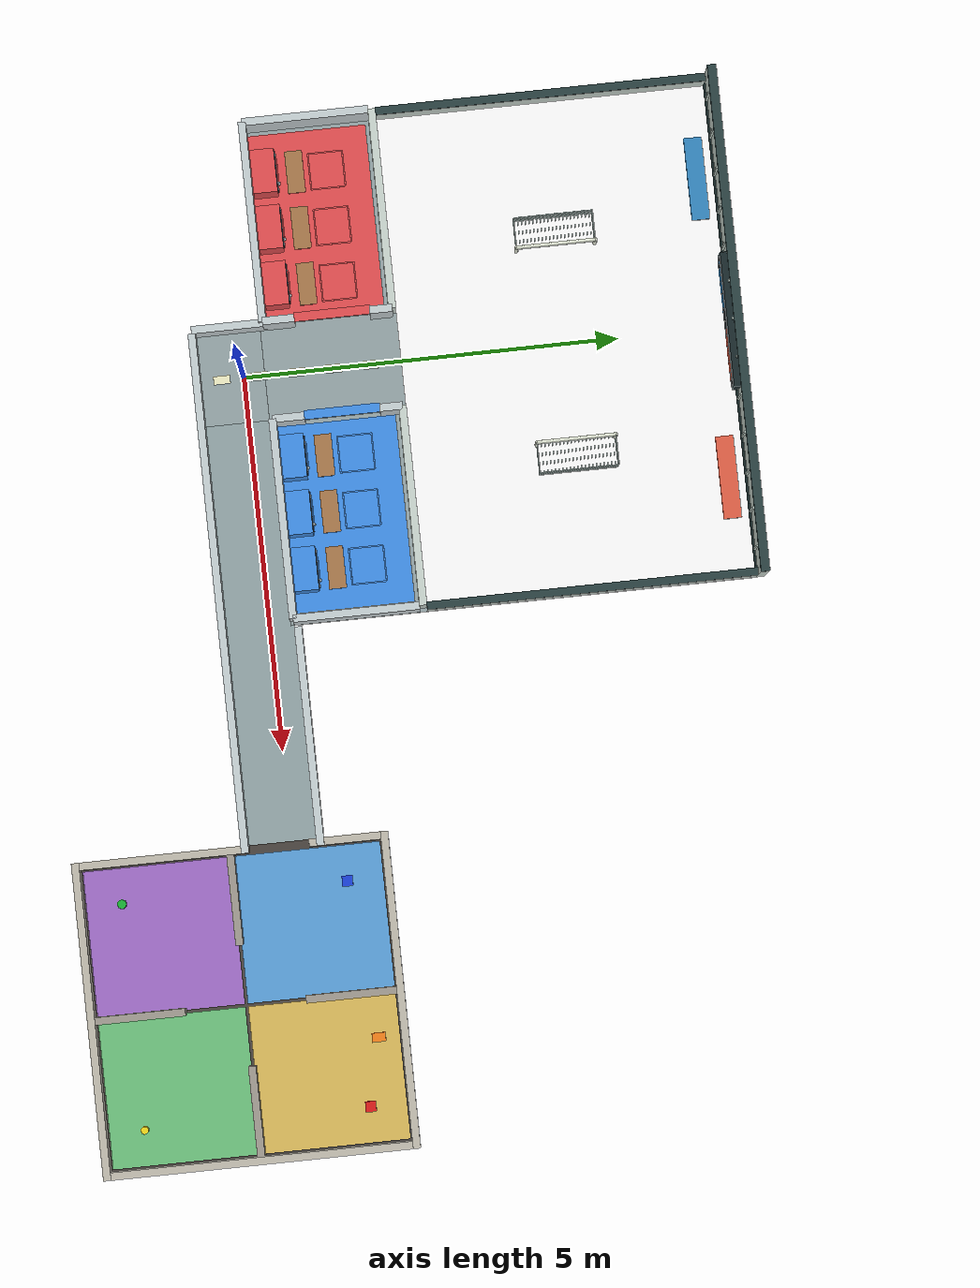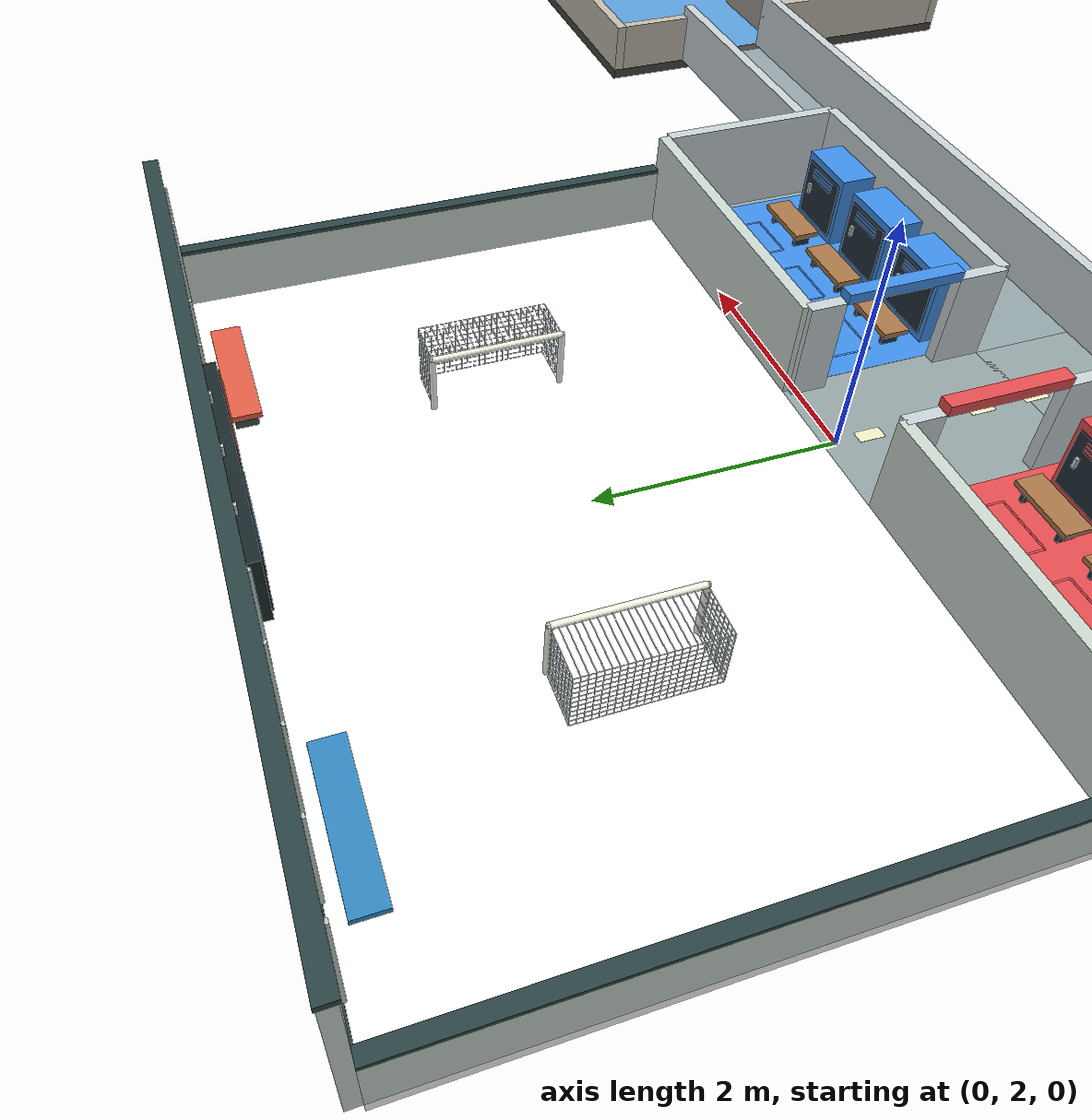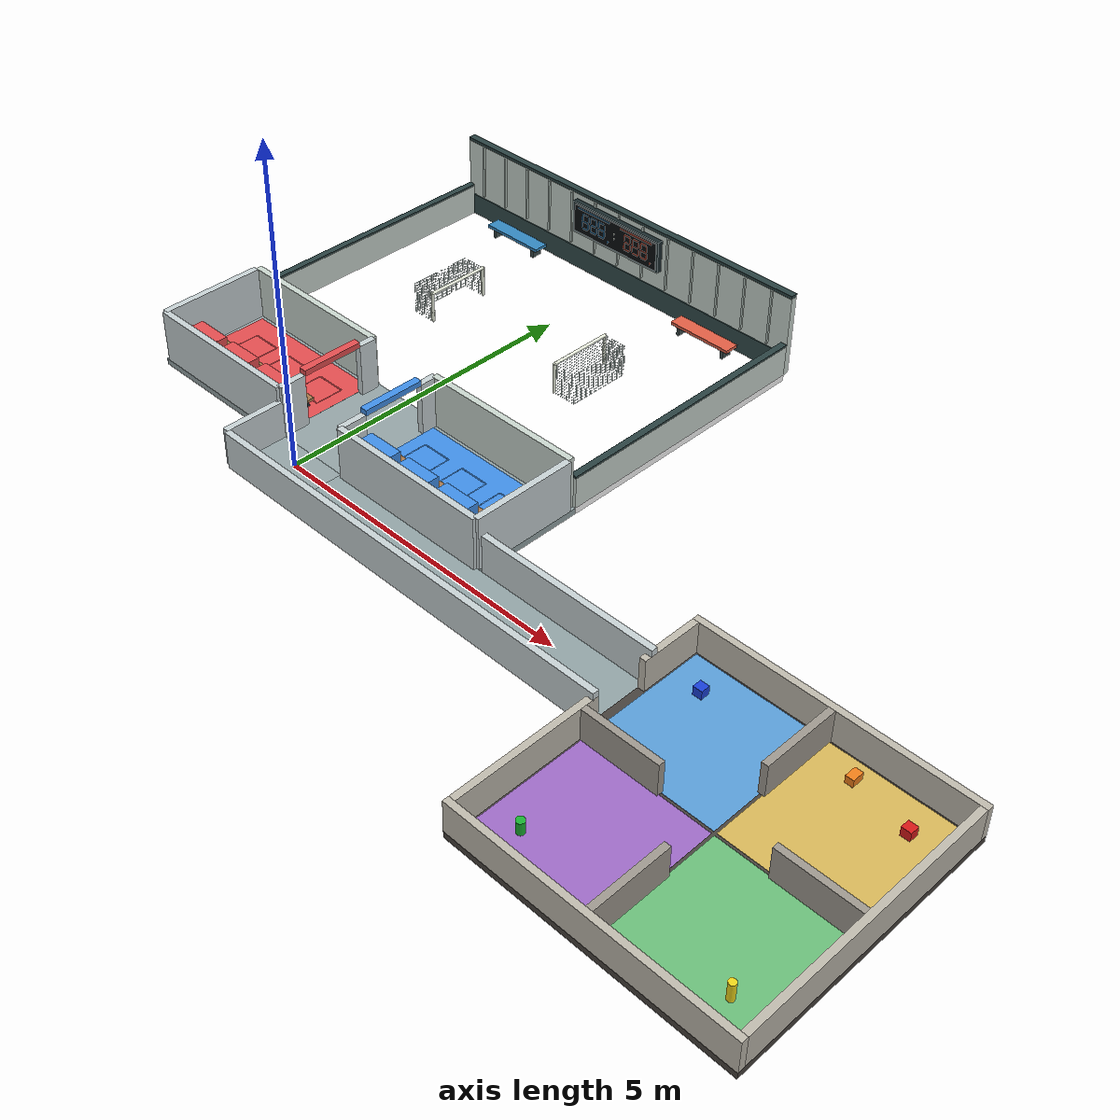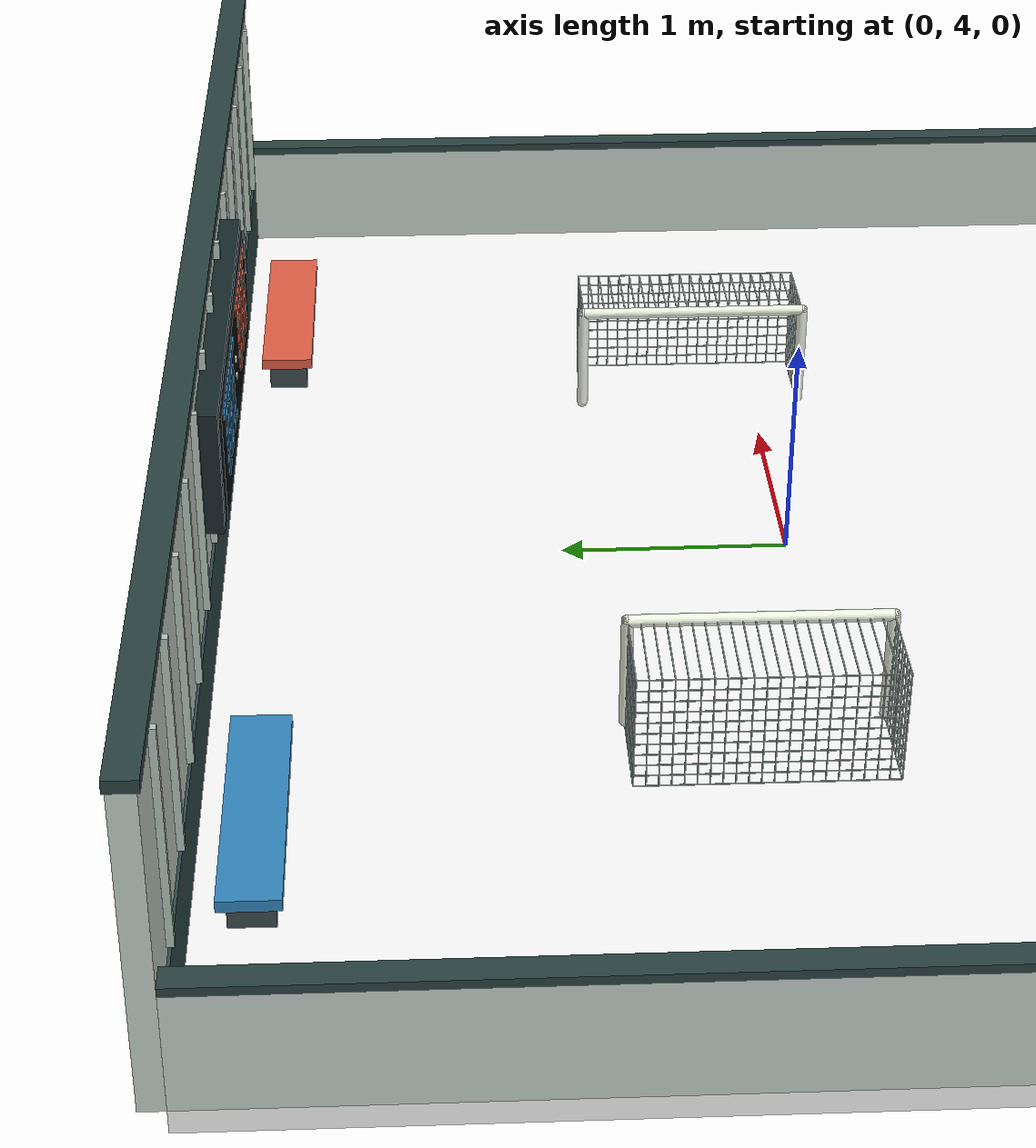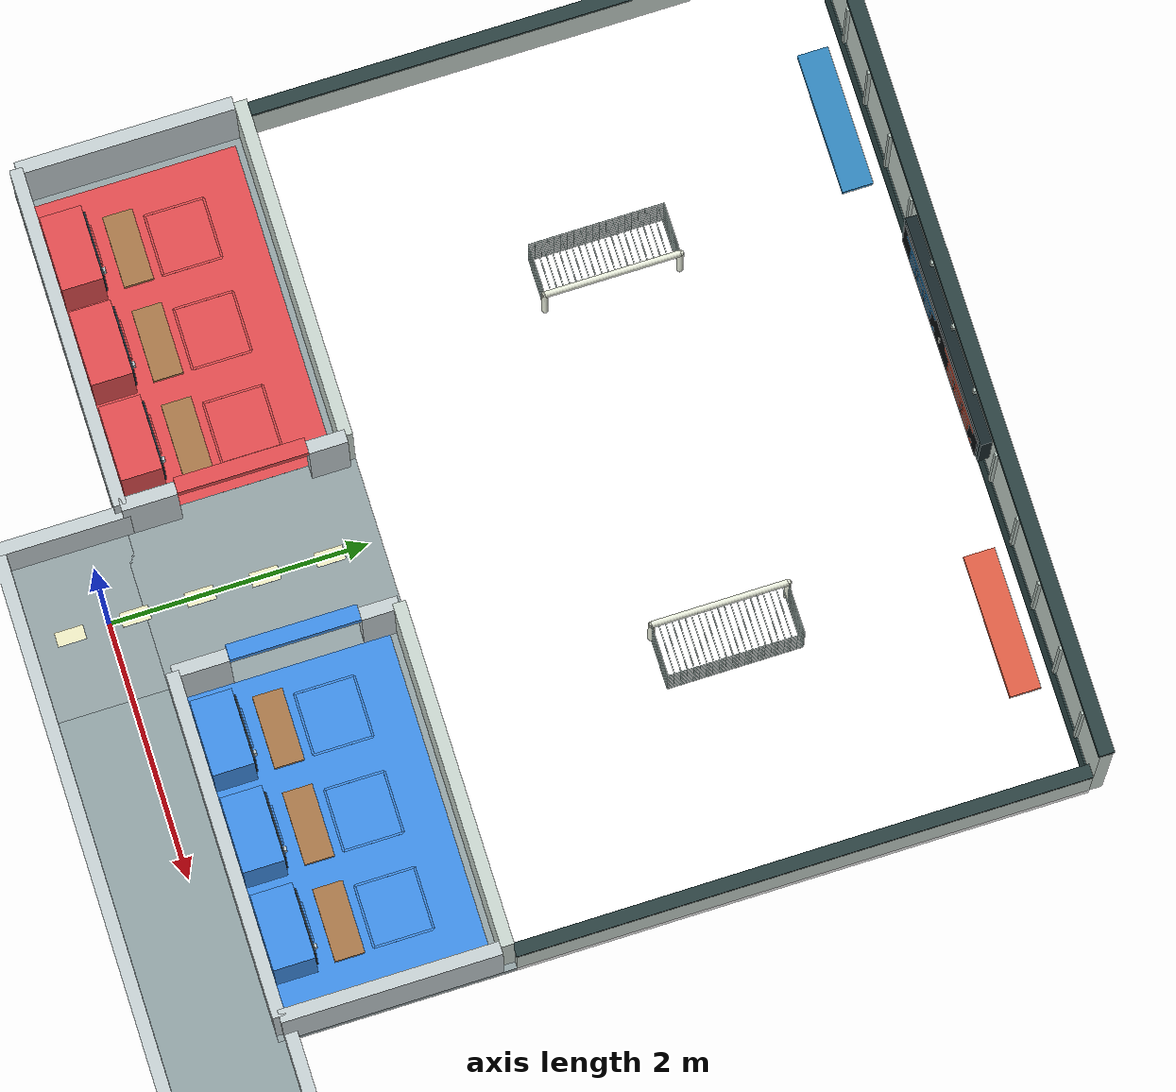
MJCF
<mujoco model="microduck_football_club">
  <include file="../benchmark/scene.xml" />
  <include file="../football/field.xml" />
  <worldbody>
    <geom name="club_floor" type="box" size="3.35 0.9125 0.05" pos="0 1.1875 -0.05" rgba="0.58 0.64 0.65 1" group="0" />
    <geom name="tunnel_floor" type="box" size="0.6 0.45 0.05" pos="0 -0.125 -0.05" rgba="0.58 0.64 0.65 1" group="0" />
    <geom name="corridor_floor" type="box" size="2.8 0.45 0.05" pos="3.4 -0.125 -0.05" rgba="0.57 0.64 0.65 1" group="0" />
    <geom name="corridor_south" type="box" size="3.45 0.05 0.3" pos="2.85 -0.625 0.3" rgba="0.78 0.82 0.83 1" group="0" />
    <geom name="corridor_north" type="box" size="1.45 0.05 0.3" pos="4.85 0.375 0.3" rgba="0.78 0.82 0.83 1" group="0" />
    <geom name="tunnel_west" type="box" size="0.05 0.5 0.3" pos="-0.65 -0.125 0.3" rgba="0.78 0.82 0.83 1" group="0" />
    <geom name="red_outer_wall" type="box" size="0.05 0.8375 0.42" pos="-3.3 1.1625 0.42" rgba="0.78 0.82 0.83 1" group="0" />
    <geom name="red_south_wall" type="box" size="1.325 0.05 0.42" pos="-1.975 0.325 0.42" rgba="0.78 0.82 0.83 1" group="0" />
    <geom name="red_inner_south" type="box" size="0.05 0.2125 0.42" pos="-0.65 0.5375 0.42" rgba="0.78 0.82 0.83 1" group="0" />
    <geom name="red_inner_north" type="box" size="0.05 0.15 0.42" pos="-0.65 1.9 0.42" rgba="0.78 0.82 0.83 1" group="0" />
    <geom name="floor_red_lockers" type="box" size="1.25 0.7875 0.001" pos="-1.95 1.1625 0.001" rgba="0.89 0.30 0.31 1" group="1" contype="0" conaffinity="0" />
    <geom name="red_door_header" type="box" size="0.06 0.5 0.045" pos="-0.65 1.25 0.88" rgba="0.89 0.30 0.31 1" group="0" />
    <geom name="red_locker_1" type="box" size="0.29 0.16 0.33" pos="-2.65 0.545 0.33" rgba="0.89 0.30 0.31 1" group="0" />
    <geom name="red_locker_inset_1" type="box" size="0.25 0.007 0.26" pos="-2.65 0.714 0.33" rgba="0.13 0.18 0.22 1" group="1" contype="0" conaffinity="0" />
    <geom name="red_locker_handle_1" type="box" size="0.015 0.015 0.045" pos="-2.49 0.73 0.35" rgba="0.75 0.80 0.82 1" group="1" contype="0" conaffinity="0" />
    <geom name="red_vent_1_0" type="box" size="0.15 0.009 0.006" pos="-2.65 0.725 0.48" rgba="0.89 0.30 0.31 1" group="1" contype="0" conaffinity="0" />
    <geom name="red_vent_1_1" type="box" size="0.15 0.009 0.006" pos="-2.65 0.725 0.515" rgba="0.89 0.30 0.31 1" group="1" contype="0" conaffinity="0" />
    <geom name="red_vent_1_2" type="box" size="0.15 0.009 0.006" pos="-2.65 0.725 0.55" rgba="0.89 0.30 0.31 1" group="1" contype="0" conaffinity="0" />
    <geom name="red_bench_1" type="box" size="0.28 0.115 0.022" pos="-2.65 0.955 0.14" rgba="0.66 0.47 0.29 1" group="0" />
    <geom name="red_bench_leg_1_-0.2" type="box" size="0.018 0.075 0.059" pos="-2.85 0.955 0.059" rgba="0.13 0.18 0.22 1" group="0" />
    <geom name="red_bench_leg_1_0.2" type="box" size="0.018 0.075 0.059" pos="-2.45 0.955 0.059" rgba="0.13 0.18 0.22 1" group="0" />
    <geom name="red_bay_1_x-1" type="box" size="0.24 0.008 0.001" pos="-2.65 1.145 0.002" rgba="0.89 0.30 0.31 1" group="1" contype="0" conaffinity="0" />
    <geom name="red_bay_1_y-1" type="box" size="0.008 0.23 0.001" pos="-2.89 1.375 0.002" rgba="0.89 0.30 0.31 1" group="1" contype="0" conaffinity="0" />
    <geom name="red_bay_1_x1" type="box" size="0.24 0.008 0.001" pos="-2.65 1.605 0.002" rgba="0.89 0.30 0.31 1" group="1" contype="0" conaffinity="0" />
    <geom name="red_bay_1_y1" type="box" size="0.008 0.23 0.001" pos="-2.41 1.375 0.002" rgba="0.89 0.30 0.31 1" group="1" contype="0" conaffinity="0" />
    <geom name="red_locker_2" type="box" size="0.29 0.16 0.33" pos="-1.9 0.545 0.33" rgba="0.89 0.30 0.31 1" group="0" />
    <geom name="red_locker_inset_2" type="box" size="0.25 0.007 0.26" pos="-1.9 0.714 0.33" rgba="0.13 0.18 0.22 1" group="1" contype="0" conaffinity="0" />
    <geom name="red_locker_handle_2" type="box" size="0.015 0.015 0.045" pos="-1.74 0.73 0.35" rgba="0.75 0.80 0.82 1" group="1" contype="0" conaffinity="0" />
    <geom name="red_vent_2_0" type="box" size="0.15 0.009 0.006" pos="-1.9 0.725 0.48" rgba="0.89 0.30 0.31 1" group="1" contype="0" conaffinity="0" />
    <geom name="red_vent_2_1" type="box" size="0.15 0.009 0.006" pos="-1.9 0.725 0.515" rgba="0.89 0.30 0.31 1" group="1" contype="0" conaffinity="0" />
    <geom name="red_vent_2_2" type="box" size="0.15 0.009 0.006" pos="-1.9 0.725 0.55" rgba="0.89 0.30 0.31 1" group="1" contype="0" conaffinity="0" />
    <geom name="red_bench_2" type="box" size="0.28 0.115 0.022" pos="-1.9 0.955 0.14" rgba="0.66 0.47 0.29 1" group="0" />
    <geom name="red_bench_leg_2_-0.2" type="box" size="0.018 0.075 0.059" pos="-2.1 0.955 0.059" rgba="0.13 0.18 0.22 1" group="0" />
    <geom name="red_bench_leg_2_0.2" type="box" size="0.018 0.075 0.059" pos="-1.7 0.955 0.059" rgba="0.13 0.18 0.22 1" group="0" />
    <geom name="red_bay_2_x-1" type="box" size="0.24 0.008 0.001" pos="-1.9 1.145 0.002" rgba="0.89 0.30 0.31 1" group="1" contype="0" conaffinity="0" />
    <geom name="red_bay_2_y-1" type="box" size="0.008 0.23 0.001" pos="-2.14 1.375 0.002" rgba="0.89 0.30 0.31 1" group="1" contype="0" conaffinity="0" />
    <geom name="red_bay_2_x1" type="box" size="0.24 0.008 0.001" pos="-1.9 1.605 0.002" rgba="0.89 0.30 0.31 1" group="1" contype="0" conaffinity="0" />
    <geom name="red_bay_2_y1" type="box" size="0.008 0.23 0.001" pos="-1.66 1.375 0.002" rgba="0.89 0.30 0.31 1" group="1" contype="0" conaffinity="0" />
    <geom name="red_locker_3" type="box" size="0.29 0.16 0.33" pos="-1.15 0.545 0.33" rgba="0.89 0.30 0.31 1" group="0" />
    <geom name="red_locker_inset_3" type="box" size="0.25 0.007 0.26" pos="-1.15 0.714 0.33" rgba="0.13 0.18 0.22 1" group="1" contype="0" conaffinity="0" />
    <geom name="red_locker_handle_3" type="box" size="0.015 0.015 0.045" pos="-0.99 0.73 0.35" rgba="0.75 0.80 0.82 1" group="1" contype="0" conaffinity="0" />
    <geom name="red_vent_3_0" type="box" size="0.15 0.009 0.006" pos="-1.15 0.725 0.48" rgba="0.89 0.30 0.31 1" group="1" contype="0" conaffinity="0" />
    <geom name="red_vent_3_1" type="box" size="0.15 0.009 0.006" pos="-1.15 0.725 0.515" rgba="0.89 0.30 0.31 1" group="1" contype="0" conaffinity="0" />
    <geom name="red_vent_3_2" type="box" size="0.15 0.009 0.006" pos="-1.15 0.725 0.55" rgba="0.89 0.30 0.31 1" group="1" contype="0" conaffinity="0" />
    <geom name="red_bench_3" type="box" size="0.28 0.115 0.022" pos="-1.15 0.955 0.14" rgba="0.66 0.47 0.29 1" group="0" />
    <geom name="red_bench_leg_3_-0.2" type="box" size="0.018 0.075 0.059" pos="-1.35 0.955 0.059" rgba="0.13 0.18 0.22 1" group="0" />
    <geom name="red_bench_leg_3_0.2" type="box" size="0.018 0.075 0.059" pos="-0.95 0.955 0.059" rgba="0.13 0.18 0.22 1" group="0" />
    <geom name="red_bay_3_x-1" type="box" size="0.24 0.008 0.001" pos="-1.15 1.145 0.002" rgba="0.89 0.30 0.31 1" group="1" contype="0" conaffinity="0" />
    <geom name="red_bay_3_y-1" type="box" size="0.008 0.23 0.001" pos="-1.39 1.375 0.002" rgba="0.89 0.30 0.31 1" group="1" contype="0" conaffinity="0" />
    <geom name="red_bay_3_x1" type="box" size="0.24 0.008 0.001" pos="-1.15 1.605 0.002" rgba="0.89 0.30 0.31 1" group="1" contype="0" conaffinity="0" />
    <geom name="red_bay_3_y1" type="box" size="0.008 0.23 0.001" pos="-0.91 1.375 0.002" rgba="0.89 0.30 0.31 1" group="1" contype="0" conaffinity="0" />
    <geom name="blue_outer_wall" type="box" size="0.05 0.8375 0.42" pos="3.3 1.1625 0.42" rgba="0.78 0.82 0.83 1" group="0" />
    <geom name="blue_south_wall" type="box" size="1.325 0.05 0.42" pos="1.975 0.325 0.42" rgba="0.78 0.82 0.83 1" group="0" />
    <geom name="blue_inner_south" type="box" size="0.05 0.2125 0.42" pos="0.65 0.5375 0.42" rgba="0.78 0.82 0.83 1" group="0" />
    <geom name="blue_inner_north" type="box" size="0.05 0.15 0.42" pos="0.65 1.9 0.42" rgba="0.78 0.82 0.83 1" group="0" />
    <geom name="floor_blue_lockers" type="box" size="1.25 0.7875 0.001" pos="1.95 1.1625 0.001" rgba="0.25 0.56 0.91 1" group="1" contype="0" conaffinity="0" />
    <geom name="blue_door_header" type="box" size="0.06 0.5 0.045" pos="0.65 1.25 0.88" rgba="0.25 0.56 0.91 1" group="0" />
    <geom name="blue_locker_1" type="box" size="0.29 0.16 0.33" pos="2.65 0.545 0.33" rgba="0.25 0.56 0.91 1" group="0" />
    <geom name="blue_locker_inset_1" type="box" size="0.25 0.007 0.26" pos="2.65 0.714 0.33" rgba="0.13 0.18 0.22 1" group="1" contype="0" conaffinity="0" />
    <geom name="blue_locker_handle_1" type="box" size="0.015 0.015 0.045" pos="2.81 0.73 0.35" rgba="0.75 0.80 0.82 1" group="1" contype="0" conaffinity="0" />
    <geom name="blue_vent_1_0" type="box" size="0.15 0.009 0.006" pos="2.65 0.725 0.48" rgba="0.25 0.56 0.91 1" group="1" contype="0" conaffinity="0" />
    <geom name="blue_vent_1_1" type="box" size="0.15 0.009 0.006" pos="2.65 0.725 0.515" rgba="0.25 0.56 0.91 1" group="1" contype="0" conaffinity="0" />
    <geom name="blue_vent_1_2" type="box" size="0.15 0.009 0.006" pos="2.65 0.725 0.55" rgba="0.25 0.56 0.91 1" group="1" contype="0" conaffinity="0" />
    <geom name="blue_bench_1" type="box" size="0.28 0.115 0.022" pos="2.65 0.955 0.14" rgba="0.66 0.47 0.29 1" group="0" />
    <geom name="blue_bench_leg_1_-0.2" type="box" size="0.018 0.075 0.059" pos="2.45 0.955 0.059" rgba="0.13 0.18 0.22 1" group="0" />
    <geom name="blue_bench_leg_1_0.2" type="box" size="0.018 0.075 0.059" pos="2.85 0.955 0.059" rgba="0.13 0.18 0.22 1" group="0" />
    <geom name="blue_bay_1_x-1" type="box" size="0.24 0.008 0.001" pos="2.65 1.145 0.002" rgba="0.25 0.56 0.91 1" group="1" contype="0" conaffinity="0" />
    <geom name="blue_bay_1_y-1" type="box" size="0.008 0.23 0.001" pos="2.41 1.375 0.002" rgba="0.25 0.56 0.91 1" group="1" contype="0" conaffinity="0" />
    <geom name="blue_bay_1_x1" type="box" size="0.24 0.008 0.001" pos="2.65 1.605 0.002" rgba="0.25 0.56 0.91 1" group="1" contype="0" conaffinity="0" />
    <geom name="blue_bay_1_y1" type="box" size="0.008 0.23 0.001" pos="2.89 1.375 0.002" rgba="0.25 0.56 0.91 1" group="1" contype="0" conaffinity="0" />
    <geom name="blue_locker_2" type="box" size="0.29 0.16 0.33" pos="1.9 0.545 0.33" rgba="0.25 0.56 0.91 1" group="0" />
    <geom name="blue_locker_inset_2" type="box" size="0.25 0.007 0.26" pos="1.9 0.714 0.33" rgba="0.13 0.18 0.22 1" group="1" contype="0" conaffinity="0" />
    <geom name="blue_locker_handle_2" type="box" size="0.015 0.015 0.045" pos="2.06 0.73 0.35" rgba="0.75 0.80 0.82 1" group="1" contype="0" conaffinity="0" />
    <geom name="blue_vent_2_0" type="box" size="0.15 0.009 0.006" pos="1.9 0.725 0.48" rgba="0.25 0.56 0.91 1" group="1" contype="0" conaffinity="0" />
    <geom name="blue_vent_2_1" type="box" size="0.15 0.009 0.006" pos="1.9 0.725 0.515" rgba="0.25 0.56 0.91 1" group="1" contype="0" conaffinity="0" />
    <geom name="blue_vent_2_2" type="box" size="0.15 0.009 0.006" pos="1.9 0.725 0.55" rgba="0.25 0.56 0.91 1" group="1" contype="0" conaffinity="0" />
    <geom name="blue_bench_2" type="box" size="0.28 0.115 0.022" pos="1.9 0.955 0.14" rgba="0.66 0.47 0.29 1" group="0" />
    <geom name="blue_bench_leg_2_-0.2" type="box" size="0.018 0.075 0.059" pos="1.7 0.955 0.059" rgba="0.13 0.18 0.22 1" group="0" />
    <geom name="blue_bench_leg_2_0.2" type="box" size="0.018 0.075 0.059" pos="2.1 0.955 0.059" rgba="0.13 0.18 0.22 1" group="0" />
    <geom name="blue_bay_2_x-1" type="box" size="0.24 0.008 0.001" pos="1.9 1.145 0.002" rgba="0.25 0.56 0.91 1" group="1" contype="0" conaffinity="0" />
    <geom name="blue_bay_2_y-1" type="box" size="0.008 0.23 0.001" pos="1.66 1.375 0.002" rgba="0.25 0.56 0.91 1" group="1" contype="0" conaffinity="0" />
    <geom name="blue_bay_2_x1" type="box" size="0.24 0.008 0.001" pos="1.9 1.605 0.002" rgba="0.25 0.56 0.91 1" group="1" contype="0" conaffinity="0" />
    <geom name="blue_bay_2_y1" type="box" size="0.008 0.23 0.001" pos="2.14 1.375 0.002" rgba="0.25 0.56 0.91 1" group="1" contype="0" conaffinity="0" />
    <geom name="blue_locker_3" type="box" size="0.29 0.16 0.33" pos="1.15 0.545 0.33" rgba="0.25 0.56 0.91 1" group="0" />
    <geom name="blue_locker_inset_3" type="box" size="0.25 0.007 0.26" pos="1.15 0.714 0.33" rgba="0.13 0.18 0.22 1" group="1" contype="0" conaffinity="0" />
    <geom name="blue_locker_handle_3" type="box" size="0.015 0.015 0.045" pos="1.31 0.73 0.35" rgba="0.75 0.80 0.82 1" group="1" contype="0" conaffinity="0" />
    <geom name="blue_vent_3_0" type="box" size="0.15 0.009 0.006" pos="1.15 0.725 0.48" rgba="0.25 0.56 0.91 1" group="1" contype="0" conaffinity="0" />
    <geom name="blue_vent_3_1" type="box" size="0.15 0.009 0.006" pos="1.15 0.725 0.515" rgba="0.25 0.56 0.91 1" group="1" contype="0" conaffinity="0" />
    <geom name="blue_vent_3_2" type="box" size="0.15 0.009 0.006" pos="1.15 0.725 0.55" rgba="0.25 0.56 0.91 1" group="1" contype="0" conaffinity="0" />
    <geom name="blue_bench_3" type="box" size="0.28 0.115 0.022" pos="1.15 0.955 0.14" rgba="0.66 0.47 0.29 1" group="0" />
    <geom name="blue_bench_leg_3_-0.2" type="box" size="0.018 0.075 0.059" pos="0.95 0.955 0.059" rgba="0.13 0.18 0.22 1" group="0" />
    <geom name="blue_bench_leg_3_0.2" type="box" size="0.018 0.075 0.059" pos="1.35 0.955 0.059" rgba="0.13 0.18 0.22 1" group="0" />
    <geom name="blue_bay_3_x-1" type="box" size="0.24 0.008 0.001" pos="1.15 1.145 0.002" rgba="0.25 0.56 0.91 1" group="1" contype="0" conaffinity="0" />
    <geom name="blue_bay_3_y-1" type="box" size="0.008 0.23 0.001" pos="0.91 1.375 0.002" rgba="0.25 0.56 0.91 1" group="1" contype="0" conaffinity="0" />
    <geom name="blue_bay_3_x1" type="box" size="0.24 0.008 0.001" pos="1.15 1.605 0.002" rgba="0.25 0.56 0.91 1" group="1" contype="0" conaffinity="0" />
    <geom name="blue_bay_3_y1" type="box" size="0.008 0.23 0.001" pos="1.39 1.375 0.002" rgba="0.25 0.56 0.91 1" group="1" contype="0" conaffinity="0" />
    <geom name="tunnel_mark_-0.3" type="box" size="0.055 0.11 0.001" pos="0 -0.3 0.002" rgba="0.94 0.93 0.77 1" group="1" contype="0" conaffinity="0" />
    <geom name="tunnel_mark_0.2" type="box" size="0.055 0.11 0.001" pos="0 0.2 0.002" rgba="0.94 0.93 0.77 1" group="1" contype="0" conaffinity="0" />
    <geom name="tunnel_mark_0.7" type="box" size="0.055 0.11 0.001" pos="0 0.7 0.002" rgba="0.94 0.93 0.77 1" group="1" contype="0" conaffinity="0" />
    <geom name="tunnel_mark_1.2" type="box" size="0.055 0.11 0.001" pos="0 1.2 0.002" rgba="0.94 0.93 0.77 1" group="1" contype="0" conaffinity="0" />
    <geom name="tunnel_mark_1.7" type="box" size="0.055 0.11 0.001" pos="0 1.7 0.002" rgba="0.94 0.93 0.77 1" group="1" contype="0" conaffinity="0" />
  </worldbody>
</mujoco>

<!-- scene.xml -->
<mujoco model="benchmark_wing">
  <visual>
    <headlight diffuse="0.6 0.6 0.6" ambient="0.3 0.3 0.3" specular="0 0 0" />
    <global azimuth="150" elevation="-25" offwidth="1280" offheight="720" />
  </visual>
  <asset>
    <texture type="skybox" builtin="gradient" rgb1="0.4 0.55 0.7" rgb2="0.05 0.05 0.1" width="512" height="3072" />
    <texture type="2d" name="floortex" builtin="checker" mark="edge" rgb1="0.32 0.3 0.28" rgb2="0.24 0.22 0.2" markrgb="0.5 0.5 0.5" width="300" height="300" />
    <material name="floormat" texture="floortex" texuniform="true" texrepeat="8 8" reflectance="0.15" />
    <material name="wallmat" rgba="0.75 0.73 0.68 1" />
    <material name="stubmat" rgba="0.62 0.6 0.56 1" />
    <material name="kitchenmat" rgba="0.85 0.72 0.35 1" />
    <material name="livingmat" rgba="0.35 0.62 0.85 1" />
    <material name="bedroommat" rgba="0.62 0.42 0.78 1" />
    <material name="officemat" rgba="0.42 0.75 0.48 1" />
  </asset>
  <worldbody>
    <body name="benchmark_wing" pos="8.3 -0.825 0">
      <light name="sun_a" pos="1.5 1.5 3.0" dir="-0.35 -0.35 -1" directional="true" diffuse="0.55 0.55 0.55" specular="0.1 0.1 0.1" />
      <light name="sun_b" pos="-1.5 -1.5 3.0" dir="0.35 0.35 -1" directional="true" diffuse="0.45 0.45 0.45" specular="0.05 0.05 0.05" />
      <geom name="floor" type="box" size="2.1 2.1 0.05" pos="0 0 -0.05" material="floormat" group="0" />
      <geom name="floor_kitchen" type="box" size="0.98 0.98 0.001" pos="1 1 0.001" material="kitchenmat" contype="0" conaffinity="0" group="0" />
      <geom name="floor_living" type="box" size="0.98 0.98 0.001" pos="-1 1 0.001" material="livingmat" contype="0" conaffinity="0" group="0" />
      <geom name="floor_bedroom" type="box" size="0.98 0.98 0.001" pos="-1 -1 0.001" material="bedroommat" contype="0" conaffinity="0" group="0" />
      <geom name="floor_office" type="box" size="0.98 0.98 0.001" pos="1 -1 0.001" material="officemat" contype="0" conaffinity="0" group="0" />
      <geom name="wall_south" type="box" size="2.1 0.05 0.25" pos="0 -2.05 0.25" material="wallmat" group="0" />
      <geom name="wall_east" type="box" size="0.05 2.0 0.25" pos="2.05 0 0.25" material="wallmat" group="0" />
      <geom name="stub_east" type="box" size="0.6 0.05 0.25" pos="1.4 0 0.25" material="stubmat" group="0" />
      <geom name="stub_west" type="box" size="0.6 0.05 0.25" pos="-1.4 0 0.25" material="stubmat" group="0" />
      <geom name="stub_north" type="box" size="0.05 0.6 0.25" pos="0 1.4 0.25" material="stubmat" group="0" />
      <geom name="stub_south" type="box" size="0.05 0.6 0.25" pos="0 -1.4 0.25" material="stubmat" group="0" />
      <geom name="red_box" type="box" size="0.07 0.07 0.07" pos="1.5 1.5 0.07" rgba="0.85 0.1 0.1 1" group="0" />
      <geom name="blue_box" type="box" size="0.07 0.07 0.07" pos="-1.5 1.5 0.07" rgba="0.1 0.25 0.85 1" group="0" />
      <geom name="green_cylinder" type="cylinder" size="0.06 0.1" pos="-1.5 -1.5 0.1" rgba="0.1 0.7 0.2 1" group="0" />
      <geom name="yellow_pillar" type="cylinder" size="0.05 0.14" pos="1.5 -1.5 0.14" rgba="0.95 0.85 0.1 1" group="0" />
      <geom name="orange_crate" type="box" size="0.06 0.09 0.06" pos="0.6 1.7 0.06" rgba="0.95 0.5 0.1 1" group="0" />
      <geom name="wall_north_west" type="box" size="2.1 0.05 0.25" pos="0 2.05 0.25" material="wallmat" group="0" />
      <geom name="wall_west" type="box" size="0.05 1.125 0.25" pos="-2.05 -0.875 0.25" material="wallmat" group="0" />
      <geom name="wall_west_upper" type="box" size="0.05 0.475 0.25" pos="-2.05 1.525 0.25" material="wallmat" group="0" />
    </body>
  </worldbody>
</mujoco>

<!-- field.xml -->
<mujoco model="microduck_football_club">
  <worldbody>
    <geom name="football_floor" type="box" size="3.35 2.2 0.05" rgba="1 1 1 1" group="0" pos="0 4.3 -0.05" material="football_surface" />
    <site name="football_goal_blue" type="box" pos="-1.306 4.3 0" size=".5 .48 .006" quat="0 0 0 1" rgba="0 0 0 0" group="5" />
    <geom name="football_blue_post_-1" type="capsule" size="0.025" rgba="0.93 0.95 0.88 1" group="0" fromto="-1.3 3.775 0.025 -1.3 3.775 0.505" />
    <geom name="football_blue_post_1" type="capsule" size="0.025" rgba="0.93 0.95 0.88 1" group="0" fromto="-1.3 4.825 0.025 -1.3 4.825 0.505" />
    <geom name="football_blue_crossbar" type="capsule" size="0.025" rgba="0.93 0.95 0.88 1" group="0" fromto="-1.3 3.775 0.505 -1.3 4.825 0.505" />
    <geom name="football_blue_net_0" type="capsule" size="0.0025" rgba="0.73 0.81 0.79 1" group="0" fromto="-1.7 3.775 0.005 -1.7 3.775 0.505" friction=".4 .005 .0001" solref=".03 1" />
    <geom name="football_blue_net_1" type="capsule" size="0.0025" rgba="0.73 0.81 0.79 1" group="0" fromto="-1.3 3.775 0.505 -1.7 3.775 0.505" friction=".4 .005 .0001" solref=".03 1" />
    <geom name="football_blue_net_2" type="capsule" size="0.0025" rgba="0.73 0.81 0.79 1" group="0" fromto="-1.7 3.825 0.005 -1.7 3.825 0.505" friction=".4 .005 .0001" solref=".03 1" />
    <geom name="football_blue_net_3" type="capsule" size="0.0025" rgba="0.73 0.81 0.79 1" group="0" fromto="-1.3 3.825 0.505 -1.7 3.825 0.505" friction=".4 .005 .0001" solref=".03 1" />
    <geom name="football_blue_net_4" type="capsule" size="0.0025" rgba="0.73 0.81 0.79 1" group="0" fromto="-1.7 3.875 0.005 -1.7 3.875 0.505" friction=".4 .005 .0001" solref=".03 1" />
    <geom name="football_blue_net_5" type="capsule" size="0.0025" rgba="0.73 0.81 0.79 1" group="0" fromto="-1.3 3.875 0.505 -1.7 3.875 0.505" friction=".4 .005 .0001" solref=".03 1" />
    <geom name="football_blue_net_6" type="capsule" size="0.0025" rgba="0.73 0.81 0.79 1" group="0" fromto="-1.7 3.925 0.005 -1.7 3.925 0.505" friction=".4 .005 .0001" solref=".03 1" />
    <geom name="football_blue_net_7" type="capsule" size="0.0025" rgba="0.73 0.81 0.79 1" group="0" fromto="-1.3 3.925 0.505 -1.7 3.925 0.505" friction=".4 .005 .0001" solref=".03 1" />
    <geom name="football_blue_net_8" type="capsule" size="0.0025" rgba="0.73 0.81 0.79 1" group="0" fromto="-1.7 3.975 0.005 -1.7 3.975 0.505" friction=".4 .005 .0001" solref=".03 1" />
    <geom name="football_blue_net_9" type="capsule" size="0.0025" rgba="0.73 0.81 0.79 1" group="0" fromto="-1.3 3.975 0.505 -1.7 3.975 0.505" friction=".4 .005 .0001" solref=".03 1" />
    <geom name="football_blue_net_10" type="capsule" size="0.0025" rgba="0.73 0.81 0.79 1" group="0" fromto="-1.7 4.025 0.005 -1.7 4.025 0.505" friction=".4 .005 .0001" solref=".03 1" />
    <geom name="football_blue_net_11" type="capsule" size="0.0025" rgba="0.73 0.81 0.79 1" group="0" fromto="-1.3 4.025 0.505 -1.7 4.025 0.505" friction=".4 .005 .0001" solref=".03 1" />
    <geom name="football_blue_net_12" type="capsule" size="0.0025" rgba="0.73 0.81 0.79 1" group="0" fromto="-1.7 4.075 0.005 -1.7 4.075 0.505" friction=".4 .005 .0001" solref=".03 1" />
    <geom name="football_blue_net_13" type="capsule" size="0.0025" rgba="0.73 0.81 0.79 1" group="0" fromto="-1.3 4.075 0.505 -1.7 4.075 0.505" friction=".4 .005 .0001" solref=".03 1" />
    <geom name="football_blue_net_14" type="capsule" size="0.0025" rgba="0.73 0.81 0.79 1" group="0" fromto="-1.7 4.125 0.005 -1.7 4.125 0.505" friction=".4 .005 .0001" solref=".03 1" />
    <geom name="football_blue_net_15" type="capsule" size="0.0025" rgba="0.73 0.81 0.79 1" group="0" fromto="-1.3 4.125 0.505 -1.7 4.125 0.505" friction=".4 .005 .0001" solref=".03 1" />
    <geom name="football_blue_net_16" type="capsule" size="0.0025" rgba="0.73 0.81 0.79 1" group="0" fromto="-1.7 4.175 0.005 -1.7 4.175 0.505" friction=".4 .005 .0001" solref=".03 1" />
    <geom name="football_blue_net_17" type="capsule" size="0.0025" rgba="0.73 0.81 0.79 1" group="0" fromto="-1.3 4.175 0.505 -1.7 4.175 0.505" friction=".4 .005 .0001" solref=".03 1" />
    <geom name="football_blue_net_18" type="capsule" size="0.0025" rgba="0.73 0.81 0.79 1" group="0" fromto="-1.7 4.225 0.005 -1.7 4.225 0.505" friction=".4 .005 .0001" solref=".03 1" />
    <geom name="football_blue_net_19" type="capsule" size="0.0025" rgba="0.73 0.81 0.79 1" group="0" fromto="-1.3 4.225 0.505 -1.7 4.225 0.505" friction=".4 .005 .0001" solref=".03 1" />
    <geom name="football_blue_net_20" type="capsule" size="0.0025" rgba="0.73 0.81 0.79 1" group="0" fromto="-1.7 4.275 0.005 -1.7 4.275 0.505" friction=".4 .005 .0001" solref=".03 1" />
    <geom name="football_blue_net_21" type="capsule" size="0.0025" rgba="0.73 0.81 0.79 1" group="0" fromto="-1.3 4.275 0.505 -1.7 4.275 0.505" friction=".4 .005 .0001" solref=".03 1" />
    <geom name="football_blue_net_22" type="capsule" size="0.0025" rgba="0.73 0.81 0.79 1" group="0" fromto="-1.7 4.325 0.005 -1.7 4.325 0.505" friction=".4 .005 .0001" solref=".03 1" />
    <geom name="football_blue_net_23" type="capsule" size="0.0025" rgba="0.73 0.81 0.79 1" group="0" fromto="-1.3 4.325 0.505 -1.7 4.325 0.505" friction=".4 .005 .0001" solref=".03 1" />
    <geom name="football_blue_net_24" type="capsule" size="0.0025" rgba="0.73 0.81 0.79 1" group="0" fromto="-1.7 4.375 0.005 -1.7 4.375 0.505" friction=".4 .005 .0001" solref=".03 1" />
    <geom name="football_blue_net_25" type="capsule" size="0.0025" rgba="0.73 0.81 0.79 1" group="0" fromto="-1.3 4.375 0.505 -1.7 4.375 0.505" friction=".4 .005 .0001" solref=".03 1" />
    <geom name="football_blue_net_26" type="capsule" size="0.0025" rgba="0.73 0.81 0.79 1" group="0" fromto="-1.7 4.425 0.005 -1.7 4.425 0.505" friction=".4 .005 .0001" solref=".03 1" />
    <geom name="football_blue_net_27" type="capsule" size="0.0025" rgba="0.73 0.81 0.79 1" group="0" fromto="-1.3 4.425 0.505 -1.7 4.425 0.505" friction=".4 .005 .0001" solref=".03 1" />
    <geom name="football_blue_net_28" type="capsule" size="0.0025" rgba="0.73 0.81 0.79 1" group="0" fromto="-1.7 4.475 0.005 -1.7 4.475 0.505" friction=".4 .005 .0001" solref=".03 1" />
    <geom name="football_blue_net_29" type="capsule" size="0.0025" rgba="0.73 0.81 0.79 1" group="0" fromto="-1.3 4.475 0.505 -1.7 4.475 0.505" friction=".4 .005 .0001" solref=".03 1" />
    <geom name="football_blue_net_30" type="capsule" size="0.0025" rgba="0.73 0.81 0.79 1" group="0" fromto="-1.7 4.525 0.005 -1.7 4.525 0.505" friction=".4 .005 .0001" solref=".03 1" />
    <geom name="football_blue_net_31" type="capsule" size="0.0025" rgba="0.73 0.81 0.79 1" group="0" fromto="-1.3 4.525 0.505 -1.7 4.525 0.505" friction=".4 .005 .0001" solref=".03 1" />
    <geom name="football_blue_net_32" type="capsule" size="0.0025" rgba="0.73 0.81 0.79 1" group="0" fromto="-1.7 4.575 0.005 -1.7 4.575 0.505" friction=".4 .005 .0001" solref=".03 1" />
    <geom name="football_blue_net_33" type="capsule" size="0.0025" rgba="0.73 0.81 0.79 1" group="0" fromto="-1.3 4.575 0.505 -1.7 4.575 0.505" friction=".4 .005 .0001" solref=".03 1" />
    <geom name="football_blue_net_34" type="capsule" size="0.0025" rgba="0.73 0.81 0.79 1" group="0" fromto="-1.7 4.625 0.005 -1.7 4.625 0.505" friction=".4 .005 .0001" solref=".03 1" />
    <geom name="football_blue_net_35" type="capsule" size="0.0025" rgba="0.73 0.81 0.79 1" group="0" fromto="-1.3 4.625 0.505 -1.7 4.625 0.505" friction=".4 .005 .0001" solref=".03 1" />
    <geom name="football_blue_net_36" type="capsule" size="0.0025" rgba="0.73 0.81 0.79 1" group="0" fromto="-1.7 4.675 0.005 -1.7 4.675 0.505" friction=".4 .005 .0001" solref=".03 1" />
    <geom name="football_blue_net_37" type="capsule" size="0.0025" rgba="0.73 0.81 0.79 1" group="0" fromto="-1.3 4.675 0.505 -1.7 4.675 0.505" friction=".4 .005 .0001" solref=".03 1" />
    <geom name="football_blue_net_38" type="capsule" size="0.0025" rgba="0.73 0.81 0.79 1" group="0" fromto="-1.7 4.725 0.005 -1.7 4.725 0.505" friction=".4 .005 .0001" solref=".03 1" />
    <geom name="football_blue_net_39" type="capsule" size="0.0025" rgba="0.73 0.81 0.79 1" group="0" fromto="-1.3 4.725 0.505 -1.7 4.725 0.505" friction=".4 .005 .0001" solref=".03 1" />
    <geom name="football_blue_net_40" type="capsule" size="0.0025" rgba="0.73 0.81 0.79 1" group="0" fromto="-1.7 4.775 0.005 -1.7 4.775 0.505" friction=".4 .005 .0001" solref=".03 1" />
    <geom name="football_blue_net_41" type="capsule" size="0.0025" rgba="0.73 0.81 0.79 1" group="0" fromto="-1.3 4.775 0.505 -1.7 4.775 0.505" friction=".4 .005 .0001" solref=".03 1" />
    <geom name="football_blue_net_42" type="capsule" size="0.0025" rgba="0.73 0.81 0.79 1" group="0" fromto="-1.7 4.825 0.005 -1.7 4.825 0.505" friction=".4 .005 .0001" solref=".03 1" />
    <geom name="football_blue_net_43" type="capsule" size="0.0025" rgba="0.73 0.81 0.79 1" group="0" fromto="-1.3 4.825 0.505 -1.7 4.825 0.505" friction=".4 .005 .0001" solref=".03 1" />
    <geom name="football_blue_net_44" type="capsule" size="0.0025" rgba="0.73 0.81 0.79 1" group="0" fromto="-1.7 3.775 0.005 -1.7 4.825 0.005" friction=".4 .005 .0001" solref=".03 1" />
    <geom name="football_blue_net_45" type="capsule" size="0.0025" rgba="0.73 0.81 0.79 1" group="0" fromto="-1.3 3.775 0.005 -1.7 3.775 0.005" friction=".4 .005 .0001" solref=".03 1" />
    <geom name="football_blue_net_46" type="capsule" size="0.0025" rgba="0.73 0.81 0.79 1" group="0" fromto="-1.3 4.825 0.005 -1.7 4.825 0.005" friction=".4 .005 .0001" solref=".03 1" />
    <geom name="football_blue_net_47" type="capsule" size="0.0025" rgba="0.73 0.81 0.79 1" group="0" fromto="-1.7 3.775 0.055 -1.7 4.825 0.055" friction=".4 .005 .0001" solref=".03 1" />
    <geom name="football_blue_net_48" type="capsule" size="0.0025" rgba="0.73 0.81 0.79 1" group="0" fromto="-1.3 3.775 0.055 -1.7 3.775 0.055" friction=".4 .005 .0001" solref=".03 1" />
    <geom name="football_blue_net_49" type="capsule" size="0.0025" rgba="0.73 0.81 0.79 1" group="0" fromto="-1.3 4.825 0.055 -1.7 4.825 0.055" friction=".4 .005 .0001" solref=".03 1" />
    <geom name="football_blue_net_50" type="capsule" size="0.0025" rgba="0.73 0.81 0.79 1" group="0" fromto="-1.7 3.775 0.105 -1.7 4.825 0.105" friction=".4 .005 .0001" solref=".03 1" />
    <geom name="football_blue_net_51" type="capsule" size="0.0025" rgba="0.73 0.81 0.79 1" group="0" fromto="-1.3 3.775 0.105 -1.7 3.775 0.105" friction=".4 .005 .0001" solref=".03 1" />
    <geom name="football_blue_net_52" type="capsule" size="0.0025" rgba="0.73 0.81 0.79 1" group="0" fromto="-1.3 4.825 0.105 -1.7 4.825 0.105" friction=".4 .005 .0001" solref=".03 1" />
    <geom name="football_blue_net_53" type="capsule" size="0.0025" rgba="0.73 0.81 0.79 1" group="0" fromto="-1.7 3.775 0.155 -1.7 4.825 0.155" friction=".4 .005 .0001" solref=".03 1" />
    <geom name="football_blue_net_54" type="capsule" size="0.0025" rgba="0.73 0.81 0.79 1" group="0" fromto="-1.3 3.775 0.155 -1.7 3.775 0.155" friction=".4 .005 .0001" solref=".03 1" />
    <geom name="football_blue_net_55" type="capsule" size="0.0025" rgba="0.73 0.81 0.79 1" group="0" fromto="-1.3 4.825 0.155 -1.7 4.825 0.155" friction=".4 .005 .0001" solref=".03 1" />
    <geom name="football_blue_net_56" type="capsule" size="0.0025" rgba="0.73 0.81 0.79 1" group="0" fromto="-1.7 3.775 0.205 -1.7 4.825 0.205" friction=".4 .005 .0001" solref=".03 1" />
    <geom name="football_blue_net_57" type="capsule" size="0.0025" rgba="0.73 0.81 0.79 1" group="0" fromto="-1.3 3.775 0.205 -1.7 3.775 0.205" friction=".4 .005 .0001" solref=".03 1" />
    <geom name="football_blue_net_58" type="capsule" size="0.0025" rgba="0.73 0.81 0.79 1" group="0" fromto="-1.3 4.825 0.205 -1.7 4.825 0.205" friction=".4 .005 .0001" solref=".03 1" />
    <geom name="football_blue_net_59" type="capsule" size="0.0025" rgba="0.73 0.81 0.79 1" group="0" fromto="-1.7 3.775 0.255 -1.7 4.825 0.255" friction=".4 .005 .0001" solref=".03 1" />
    <geom name="football_blue_net_60" type="capsule" size="0.0025" rgba="0.73 0.81 0.79 1" group="0" fromto="-1.3 3.775 0.255 -1.7 3.775 0.255" friction=".4 .005 .0001" solref=".03 1" />
    <geom name="football_blue_net_61" type="capsule" size="0.0025" rgba="0.73 0.81 0.79 1" group="0" fromto="-1.3 4.825 0.255 -1.7 4.825 0.255" friction=".4 .005 .0001" solref=".03 1" />
    <geom name="football_blue_net_62" type="capsule" size="0.0025" rgba="0.73 0.81 0.79 1" group="0" fromto="-1.7 3.775 0.305 -1.7 4.825 0.305" friction=".4 .005 .0001" solref=".03 1" />
    <geom name="football_blue_net_63" type="capsule" size="0.0025" rgba="0.73 0.81 0.79 1" group="0" fromto="-1.3 3.775 0.305 -1.7 3.775 0.305" friction=".4 .005 .0001" solref=".03 1" />
    <geom name="football_blue_net_64" type="capsule" size="0.0025" rgba="0.73 0.81 0.79 1" group="0" fromto="-1.3 4.825 0.305 -1.7 4.825 0.305" friction=".4 .005 .0001" solref=".03 1" />
    <geom name="football_blue_net_65" type="capsule" size="0.0025" rgba="0.73 0.81 0.79 1" group="0" fromto="-1.7 3.775 0.355 -1.7 4.825 0.355" friction=".4 .005 .0001" solref=".03 1" />
    <geom name="football_blue_net_66" type="capsule" size="0.0025" rgba="0.73 0.81 0.79 1" group="0" fromto="-1.3 3.775 0.355 -1.7 3.775 0.355" friction=".4 .005 .0001" solref=".03 1" />
    <geom name="football_blue_net_67" type="capsule" size="0.0025" rgba="0.73 0.81 0.79 1" group="0" fromto="-1.3 4.825 0.355 -1.7 4.825 0.355" friction=".4 .005 .0001" solref=".03 1" />
    <geom name="football_blue_net_68" type="capsule" size="0.0025" rgba="0.73 0.81 0.79 1" group="0" fromto="-1.7 3.775 0.405 -1.7 4.825 0.405" friction=".4 .005 .0001" solref=".03 1" />
    <geom name="football_blue_net_69" type="capsule" size="0.0025" rgba="0.73 0.81 0.79 1" group="0" fromto="-1.3 3.775 0.405 -1.7 3.775 0.405" friction=".4 .005 .0001" solref=".03 1" />
    <geom name="football_blue_net_70" type="capsule" size="0.0025" rgba="0.73 0.81 0.79 1" group="0" fromto="-1.3 4.825 0.405 -1.7 4.825 0.405" friction=".4 .005 .0001" solref=".03 1" />
    <geom name="football_blue_net_71" type="capsule" size="0.0025" rgba="0.73 0.81 0.79 1" group="0" fromto="-1.7 3.775 0.455 -1.7 4.825 0.455" friction=".4 .005 .0001" solref=".03 1" />
    <geom name="football_blue_net_72" type="capsule" size="0.0025" rgba="0.73 0.81 0.79 1" group="0" fromto="-1.3 3.775 0.455 -1.7 3.775 0.455" friction=".4 .005 .0001" solref=".03 1" />
    <geom name="football_blue_net_73" type="capsule" size="0.0025" rgba="0.73 0.81 0.79 1" group="0" fromto="-1.3 4.825 0.455 -1.7 4.825 0.455" friction=".4 .005 .0001" solref=".03 1" />
    <geom name="football_blue_net_74" type="capsule" size="0.0025" rgba="0.73 0.81 0.79 1" group="0" fromto="-1.7 3.775 0.505 -1.7 4.825 0.505" friction=".4 .005 .0001" solref=".03 1" />
    <geom name="football_blue_net_75" type="capsule" size="0.0025" rgba="0.73 0.81 0.79 1" group="0" fromto="-1.3 3.775 0.505 -1.7 3.775 0.505" friction=".4 .005 .0001" solref=".03 1" />
    <geom name="football_blue_net_76" type="capsule" size="0.0025" rgba="0.73 0.81 0.79 1" group="0" fromto="-1.3 4.825 0.505 -1.7 4.825 0.505" friction=".4 .005 .0001" solref=".03 1" />
    <geom name="football_blue_net_77" type="capsule" size="0.0025" rgba="0.73 0.81 0.79 1" group="0" fromto="-1.35 3.775 0.005 -1.35 3.775 0.505" friction=".4 .005 .0001" solref=".03 1" />
    <geom name="football_blue_net_78" type="capsule" size="0.0025" rgba="0.73 0.81 0.79 1" group="0" fromto="-1.4 3.775 0.005 -1.4 3.775 0.505" friction=".4 .005 .0001" solref=".03 1" />
    <geom name="football_blue_net_79" type="capsule" size="0.0025" rgba="0.73 0.81 0.79 1" group="0" fromto="-1.45 3.775 0.005 -1.45 3.775 0.505" friction=".4 .005 .0001" solref=".03 1" />
    <geom name="football_blue_net_80" type="capsule" size="0.0025" rgba="0.73 0.81 0.79 1" group="0" fromto="-1.5 3.775 0.005 -1.5 3.775 0.505" friction=".4 .005 .0001" solref=".03 1" />
    <geom name="football_blue_net_81" type="capsule" size="0.0025" rgba="0.73 0.81 0.79 1" group="0" fromto="-1.55 3.775 0.005 -1.55 3.775 0.505" friction=".4 .005 .0001" solref=".03 1" />
    <geom name="football_blue_net_82" type="capsule" size="0.0025" rgba="0.73 0.81 0.79 1" group="0" fromto="-1.6 3.775 0.005 -1.6 3.775 0.505" friction=".4 .005 .0001" solref=".03 1" />
    <geom name="football_blue_net_83" type="capsule" size="0.0025" rgba="0.73 0.81 0.79 1" group="0" fromto="-1.65 3.775 0.005 -1.65 3.775 0.505" friction=".4 .005 .0001" solref=".03 1" />
    <geom name="football_blue_net_84" type="capsule" size="0.0025" rgba="0.73 0.81 0.79 1" group="0" fromto="-1.35 4.825 0.005 -1.35 4.825 0.505" friction=".4 .005 .0001" solref=".03 1" />
    <geom name="football_blue_net_85" type="capsule" size="0.0025" rgba="0.73 0.81 0.79 1" group="0" fromto="-1.4 4.825 0.005 -1.4 4.825 0.505" friction=".4 .005 .0001" solref=".03 1" />
    <geom name="football_blue_net_86" type="capsule" size="0.0025" rgba="0.73 0.81 0.79 1" group="0" fromto="-1.45 4.825 0.005 -1.45 4.825 0.505" friction=".4 .005 .0001" solref=".03 1" />
    <geom name="football_blue_net_87" type="capsule" size="0.0025" rgba="0.73 0.81 0.79 1" group="0" fromto="-1.5 4.825 0.005 -1.5 4.825 0.505" friction=".4 .005 .0001" solref=".03 1" />
    <geom name="football_blue_net_88" type="capsule" size="0.0025" rgba="0.73 0.81 0.79 1" group="0" fromto="-1.55 4.825 0.005 -1.55 4.825 0.505" friction=".4 .005 .0001" solref=".03 1" />
    <geom name="football_blue_net_89" type="capsule" size="0.0025" rgba="0.73 0.81 0.79 1" group="0" fromto="-1.6 4.825 0.005 -1.6 4.825 0.505" friction=".4 .005 .0001" solref=".03 1" />
    <geom name="football_blue_net_90" type="capsule" size="0.0025" rgba="0.73 0.81 0.79 1" group="0" fromto="-1.65 4.825 0.005 -1.65 4.825 0.505" friction=".4 .005 .0001" solref=".03 1" />
    <site name="football_goal_coral" type="box" pos="1.306 4.3 0" size=".5 .48 .006" quat="1 0 0 0" rgba="0 0 0 0" group="5" />
    <geom name="football_coral_post_-1" type="capsule" size="0.025" rgba="0.93 0.95 0.88 1" group="0" fromto="1.3 3.775 0.025 1.3 3.775 0.505" />
    <geom name="football_coral_post_1" type="capsule" size="0.025" rgba="0.93 0.95 0.88 1" group="0" fromto="1.3 4.825 0.025 1.3 4.825 0.505" />
    <geom name="football_coral_crossbar" type="capsule" size="0.025" rgba="0.93 0.95 0.88 1" group="0" fromto="1.3 3.775 0.505 1.3 4.825 0.505" />
    <geom name="football_coral_net_0" type="capsule" size="0.0025" rgba="0.73 0.81 0.79 1" group="0" fromto="1.7 3.775 0.005 1.7 3.775 0.505" friction=".4 .005 .0001" solref=".03 1" />
    <geom name="football_coral_net_1" type="capsule" size="0.0025" rgba="0.73 0.81 0.79 1" group="0" fromto="1.3 3.775 0.505 1.7 3.775 0.505" friction=".4 .005 .0001" solref=".03 1" />
    <geom name="football_coral_net_2" type="capsule" size="0.0025" rgba="0.73 0.81 0.79 1" group="0" fromto="1.7 3.825 0.005 1.7 3.825 0.505" friction=".4 .005 .0001" solref=".03 1" />
    <geom name="football_coral_net_3" type="capsule" size="0.0025" rgba="0.73 0.81 0.79 1" group="0" fromto="1.3 3.825 0.505 1.7 3.825 0.505" friction=".4 .005 .0001" solref=".03 1" />
    <geom name="football_coral_net_4" type="capsule" size="0.0025" rgba="0.73 0.81 0.79 1" group="0" fromto="1.7 3.875 0.005 1.7 3.875 0.505" friction=".4 .005 .0001" solref=".03 1" />
    <geom name="football_coral_net_5" type="capsule" size="0.0025" rgba="0.73 0.81 0.79 1" group="0" fromto="1.3 3.875 0.505 1.7 3.875 0.505" friction=".4 .005 .0001" solref=".03 1" />
    <geom name="football_coral_net_6" type="capsule" size="0.0025" rgba="0.73 0.81 0.79 1" group="0" fromto="1.7 3.925 0.005 1.7 3.925 0.505" friction=".4 .005 .0001" solref=".03 1" />
    <geom name="football_coral_net_7" type="capsule" size="0.0025" rgba="0.73 0.81 0.79 1" group="0" fromto="1.3 3.925 0.505 1.7 3.925 0.505" friction=".4 .005 .0001" solref=".03 1" />
    <geom name="football_coral_net_8" type="capsule" size="0.0025" rgba="0.73 0.81 0.79 1" group="0" fromto="1.7 3.975 0.005 1.7 3.975 0.505" friction=".4 .005 .0001" solref=".03 1" />
    <geom name="football_coral_net_9" type="capsule" size="0.0025" rgba="0.73 0.81 0.79 1" group="0" fromto="1.3 3.975 0.505 1.7 3.975 0.505" friction=".4 .005 .0001" solref=".03 1" />
    <geom name="football_coral_net_10" type="capsule" size="0.0025" rgba="0.73 0.81 0.79 1" group="0" fromto="1.7 4.025 0.005 1.7 4.025 0.505" friction=".4 .005 .0001" solref=".03 1" />
    <geom name="football_coral_net_11" type="capsule" size="0.0025" rgba="0.73 0.81 0.79 1" group="0" fromto="1.3 4.025 0.505 1.7 4.025 0.505" friction=".4 .005 .0001" solref=".03 1" />
    <geom name="football_coral_net_12" type="capsule" size="0.0025" rgba="0.73 0.81 0.79 1" group="0" fromto="1.7 4.075 0.005 1.7 4.075 0.505" friction=".4 .005 .0001" solref=".03 1" />
    <geom name="football_coral_net_13" type="capsule" size="0.0025" rgba="0.73 0.81 0.79 1" group="0" fromto="1.3 4.075 0.505 1.7 4.075 0.505" friction=".4 .005 .0001" solref=".03 1" />
    <geom name="football_coral_net_14" type="capsule" size="0.0025" rgba="0.73 0.81 0.79 1" group="0" fromto="1.7 4.125 0.005 1.7 4.125 0.505" friction=".4 .005 .0001" solref=".03 1" />
    <geom name="football_coral_net_15" type="capsule" size="0.0025" rgba="0.73 0.81 0.79 1" group="0" fromto="1.3 4.125 0.505 1.7 4.125 0.505" friction=".4 .005 .0001" solref=".03 1" />
    <geom name="football_coral_net_16" type="capsule" size="0.0025" rgba="0.73 0.81 0.79 1" group="0" fromto="1.7 4.175 0.005 1.7 4.175 0.505" friction=".4 .005 .0001" solref=".03 1" />
    <geom name="football_coral_net_17" type="capsule" size="0.0025" rgba="0.73 0.81 0.79 1" group="0" fromto="1.3 4.175 0.505 1.7 4.175 0.505" friction=".4 .005 .0001" solref=".03 1" />
    <geom name="football_coral_net_18" type="capsule" size="0.0025" rgba="0.73 0.81 0.79 1" group="0" fromto="1.7 4.225 0.005 1.7 4.225 0.505" friction=".4 .005 .0001" solref=".03 1" />
    <geom name="football_coral_net_19" type="capsule" size="0.0025" rgba="0.73 0.81 0.79 1" group="0" fromto="1.3 4.225 0.505 1.7 4.225 0.505" friction=".4 .005 .0001" solref=".03 1" />
    <geom name="football_coral_net_20" type="capsule" size="0.0025" rgba="0.73 0.81 0.79 1" group="0" fromto="1.7 4.275 0.005 1.7 4.275 0.505" friction=".4 .005 .0001" solref=".03 1" />
    <geom name="football_coral_net_21" type="capsule" size="0.0025" rgba="0.73 0.81 0.79 1" group="0" fromto="1.3 4.275 0.505 1.7 4.275 0.505" friction=".4 .005 .0001" solref=".03 1" />
    <geom name="football_coral_net_22" type="capsule" size="0.0025" rgba="0.73 0.81 0.79 1" group="0" fromto="1.7 4.325 0.005 1.7 4.325 0.505" friction=".4 .005 .0001" solref=".03 1" />
    <geom name="football_coral_net_23" type="capsule" size="0.0025" rgba="0.73 0.81 0.79 1" group="0" fromto="1.3 4.325 0.505 1.7 4.325 0.505" friction=".4 .005 .0001" solref=".03 1" />
    <geom name="football_coral_net_24" type="capsule" size="0.0025" rgba="0.73 0.81 0.79 1" group="0" fromto="1.7 4.375 0.005 1.7 4.375 0.505" friction=".4 .005 .0001" solref=".03 1" />
    <geom name="football_coral_net_25" type="capsule" size="0.0025" rgba="0.73 0.81 0.79 1" group="0" fromto="1.3 4.375 0.505 1.7 4.375 0.505" friction=".4 .005 .0001" solref=".03 1" />
    <geom name="football_coral_net_26" type="capsule" size="0.0025" rgba="0.73 0.81 0.79 1" group="0" fromto="1.7 4.425 0.005 1.7 4.425 0.505" friction=".4 .005 .0001" solref=".03 1" />
    <geom name="football_coral_net_27" type="capsule" size="0.0025" rgba="0.73 0.81 0.79 1" group="0" fromto="1.3 4.425 0.505 1.7 4.425 0.505" friction=".4 .005 .0001" solref=".03 1" />
    <geom name="football_coral_net_28" type="capsule" size="0.0025" rgba="0.73 0.81 0.79 1" group="0" fromto="1.7 4.475 0.005 1.7 4.475 0.505" friction=".4 .005 .0001" solref=".03 1" />
    <geom name="football_coral_net_29" type="capsule" size="0.0025" rgba="0.73 0.81 0.79 1" group="0" fromto="1.3 4.475 0.505 1.7 4.475 0.505" friction=".4 .005 .0001" solref=".03 1" />
    <geom name="football_coral_net_30" type="capsule" size="0.0025" rgba="0.73 0.81 0.79 1" group="0" fromto="1.7 4.525 0.005 1.7 4.525 0.505" friction=".4 .005 .0001" solref=".03 1" />
    <geom name="football_coral_net_31" type="capsule" size="0.0025" rgba="0.73 0.81 0.79 1" group="0" fromto="1.3 4.525 0.505 1.7 4.525 0.505" friction=".4 .005 .0001" solref=".03 1" />
    <geom name="football_coral_net_32" type="capsule" size="0.0025" rgba="0.73 0.81 0.79 1" group="0" fromto="1.7 4.575 0.005 1.7 4.575 0.505" friction=".4 .005 .0001" solref=".03 1" />
    <geom name="football_coral_net_33" type="capsule" size="0.0025" rgba="0.73 0.81 0.79 1" group="0" fromto="1.3 4.575 0.505 1.7 4.575 0.505" friction=".4 .005 .0001" solref=".03 1" />
    <geom name="football_coral_net_34" type="capsule" size="0.0025" rgba="0.73 0.81 0.79 1" group="0" fromto="1.7 4.625 0.005 1.7 4.625 0.505" friction=".4 .005 .0001" solref=".03 1" />
    <geom name="football_coral_net_35" type="capsule" size="0.0025" rgba="0.73 0.81 0.79 1" group="0" fromto="1.3 4.625 0.505 1.7 4.625 0.505" friction=".4 .005 .0001" solref=".03 1" />
    <geom name="football_coral_net_36" type="capsule" size="0.0025" rgba="0.73 0.81 0.79 1" group="0" fromto="1.7 4.675 0.005 1.7 4.675 0.505" friction=".4 .005 .0001" solref=".03 1" />
    <geom name="football_coral_net_37" type="capsule" size="0.0025" rgba="0.73 0.81 0.79 1" group="0" fromto="1.3 4.675 0.505 1.7 4.675 0.505" friction=".4 .005 .0001" solref=".03 1" />
    <geom name="football_coral_net_38" type="capsule" size="0.0025" rgba="0.73 0.81 0.79 1" group="0" fromto="1.7 4.725 0.005 1.7 4.725 0.505" friction=".4 .005 .0001" solref=".03 1" />
    <geom name="football_coral_net_39" type="capsule" size="0.0025" rgba="0.73 0.81 0.79 1" group="0" fromto="1.3 4.725 0.505 1.7 4.725 0.505" friction=".4 .005 .0001" solref=".03 1" />
    <geom name="football_coral_net_40" type="capsule" size="0.0025" rgba="0.73 0.81 0.79 1" group="0" fromto="1.7 4.775 0.005 1.7 4.775 0.505" friction=".4 .005 .0001" solref=".03 1" />
    <geom name="football_coral_net_41" type="capsule" size="0.0025" rgba="0.73 0.81 0.79 1" group="0" fromto="1.3 4.775 0.505 1.7 4.775 0.505" friction=".4 .005 .0001" solref=".03 1" />
    <geom name="football_coral_net_42" type="capsule" size="0.0025" rgba="0.73 0.81 0.79 1" group="0" fromto="1.7 4.825 0.005 1.7 4.825 0.505" friction=".4 .005 .0001" solref=".03 1" />
    <geom name="football_coral_net_43" type="capsule" size="0.0025" rgba="0.73 0.81 0.79 1" group="0" fromto="1.3 4.825 0.505 1.7 4.825 0.505" friction=".4 .005 .0001" solref=".03 1" />
    <geom name="football_coral_net_44" type="capsule" size="0.0025" rgba="0.73 0.81 0.79 1" group="0" fromto="1.7 3.775 0.005 1.7 4.825 0.005" friction=".4 .005 .0001" solref=".03 1" />
    <geom name="football_coral_net_45" type="capsule" size="0.0025" rgba="0.73 0.81 0.79 1" group="0" fromto="1.3 3.775 0.005 1.7 3.775 0.005" friction=".4 .005 .0001" solref=".03 1" />
    <geom name="football_coral_net_46" type="capsule" size="0.0025" rgba="0.73 0.81 0.79 1" group="0" fromto="1.3 4.825 0.005 1.7 4.825 0.005" friction=".4 .005 .0001" solref=".03 1" />
    <geom name="football_coral_net_47" type="capsule" size="0.0025" rgba="0.73 0.81 0.79 1" group="0" fromto="1.7 3.775 0.055 1.7 4.825 0.055" friction=".4 .005 .0001" solref=".03 1" />
    <geom name="football_coral_net_48" type="capsule" size="0.0025" rgba="0.73 0.81 0.79 1" group="0" fromto="1.3 3.775 0.055 1.7 3.775 0.055" friction=".4 .005 .0001" solref=".03 1" />
    <geom name="football_coral_net_49" type="capsule" size="0.0025" rgba="0.73 0.81 0.79 1" group="0" fromto="1.3 4.825 0.055 1.7 4.825 0.055" friction=".4 .005 .0001" solref=".03 1" />
    <geom name="football_coral_net_50" type="capsule" size="0.0025" rgba="0.73 0.81 0.79 1" group="0" fromto="1.7 3.775 0.105 1.7 4.825 0.105" friction=".4 .005 .0001" solref=".03 1" />
    <geom name="football_coral_net_51" type="capsule" size="0.0025" rgba="0.73 0.81 0.79 1" group="0" fromto="1.3 3.775 0.105 1.7 3.775 0.105" friction=".4 .005 .0001" solref=".03 1" />
    <geom name="football_coral_net_52" type="capsule" size="0.0025" rgba="0.73 0.81 0.79 1" group="0" fromto="1.3 4.825 0.105 1.7 4.825 0.105" friction=".4 .005 .0001" solref=".03 1" />
    <geom name="football_coral_net_53" type="capsule" size="0.0025" rgba="0.73 0.81 0.79 1" group="0" fromto="1.7 3.775 0.155 1.7 4.825 0.155" friction=".4 .005 .0001" solref=".03 1" />
    <geom name="football_coral_net_54" type="capsule" size="0.0025" rgba="0.73 0.81 0.79 1" group="0" fromto="1.3 3.775 0.155 1.7 3.775 0.155" friction=".4 .005 .0001" solref=".03 1" />
    <geom name="football_coral_net_55" type="capsule" size="0.0025" rgba="0.73 0.81 0.79 1" group="0" fromto="1.3 4.825 0.155 1.7 4.825 0.155" friction=".4 .005 .0001" solref=".03 1" />
    <geom name="football_coral_net_56" type="capsule" size="0.0025" rgba="0.73 0.81 0.79 1" group="0" fromto="1.7 3.775 0.205 1.7 4.825 0.205" friction=".4 .005 .0001" solref=".03 1" />
    <geom name="football_coral_net_57" type="capsule" size="0.0025" rgba="0.73 0.81 0.79 1" group="0" fromto="1.3 3.775 0.205 1.7 3.775 0.205" friction=".4 .005 .0001" solref=".03 1" />
    <geom name="football_coral_net_58" type="capsule" size="0.0025" rgba="0.73 0.81 0.79 1" group="0" fromto="1.3 4.825 0.205 1.7 4.825 0.205" friction=".4 .005 .0001" solref=".03 1" />
    <geom name="football_coral_net_59" type="capsule" size="0.0025" rgba="0.73 0.81 0.79 1" group="0" fromto="1.7 3.775 0.255 1.7 4.825 0.255" friction=".4 .005 .0001" solref=".03 1" />
    <geom name="football_coral_net_60" type="capsule" size="0.0025" rgba="0.73 0.81 0.79 1" group="0" fromto="1.3 3.775 0.255 1.7 3.775 0.255" friction=".4 .005 .0001" solref=".03 1" />
    <geom name="football_coral_net_61" type="capsule" size="0.0025" rgba="0.73 0.81 0.79 1" group="0" fromto="1.3 4.825 0.255 1.7 4.825 0.255" friction=".4 .005 .0001" solref=".03 1" />
    <geom name="football_coral_net_62" type="capsule" size="0.0025" rgba="0.73 0.81 0.79 1" group="0" fromto="1.7 3.775 0.305 1.7 4.825 0.305" friction=".4 .005 .0001" solref=".03 1" />
    <geom name="football_coral_net_63" type="capsule" size="0.0025" rgba="0.73 0.81 0.79 1" group="0" fromto="1.3 3.775 0.305 1.7 3.775 0.305" friction=".4 .005 .0001" solref=".03 1" />
    <geom name="football_coral_net_64" type="capsule" size="0.0025" rgba="0.73 0.81 0.79 1" group="0" fromto="1.3 4.825 0.305 1.7 4.825 0.305" friction=".4 .005 .0001" solref=".03 1" />
    <geom name="football_coral_net_65" type="capsule" size="0.0025" rgba="0.73 0.81 0.79 1" group="0" fromto="1.7 3.775 0.355 1.7 4.825 0.355" friction=".4 .005 .0001" solref=".03 1" />
    <geom name="football_coral_net_66" type="capsule" size="0.0025" rgba="0.73 0.81 0.79 1" group="0" fromto="1.3 3.775 0.355 1.7 3.775 0.355" friction=".4 .005 .0001" solref=".03 1" />
    <geom name="football_coral_net_67" type="capsule" size="0.0025" rgba="0.73 0.81 0.79 1" group="0" fromto="1.3 4.825 0.355 1.7 4.825 0.355" friction=".4 .005 .0001" solref=".03 1" />
    <geom name="football_coral_net_68" type="capsule" size="0.0025" rgba="0.73 0.81 0.79 1" group="0" fromto="1.7 3.775 0.405 1.7 4.825 0.405" friction=".4 .005 .0001" solref=".03 1" />
    <geom name="football_coral_net_69" type="capsule" size="0.0025" rgba="0.73 0.81 0.79 1" group="0" fromto="1.3 3.775 0.405 1.7 3.775 0.405" friction=".4 .005 .0001" solref=".03 1" />
    <geom name="football_coral_net_70" type="capsule" size="0.0025" rgba="0.73 0.81 0.79 1" group="0" fromto="1.3 4.825 0.405 1.7 4.825 0.405" friction=".4 .005 .0001" solref=".03 1" />
    <geom name="football_coral_net_71" type="capsule" size="0.0025" rgba="0.73 0.81 0.79 1" group="0" fromto="1.7 3.775 0.455 1.7 4.825 0.455" friction=".4 .005 .0001" solref=".03 1" />
    <geom name="football_coral_net_72" type="capsule" size="0.0025" rgba="0.73 0.81 0.79 1" group="0" fromto="1.3 3.775 0.455 1.7 3.775 0.455" friction=".4 .005 .0001" solref=".03 1" />
    <geom name="football_coral_net_73" type="capsule" size="0.0025" rgba="0.73 0.81 0.79 1" group="0" fromto="1.3 4.825 0.455 1.7 4.825 0.455" friction=".4 .005 .0001" solref=".03 1" />
    <geom name="football_coral_net_74" type="capsule" size="0.0025" rgba="0.73 0.81 0.79 1" group="0" fromto="1.7 3.775 0.505 1.7 4.825 0.505" friction=".4 .005 .0001" solref=".03 1" />
    <geom name="football_coral_net_75" type="capsule" size="0.0025" rgba="0.73 0.81 0.79 1" group="0" fromto="1.3 3.775 0.505 1.7 3.775 0.505" friction=".4 .005 .0001" solref=".03 1" />
    <geom name="football_coral_net_76" type="capsule" size="0.0025" rgba="0.73 0.81 0.79 1" group="0" fromto="1.3 4.825 0.505 1.7 4.825 0.505" friction=".4 .005 .0001" solref=".03 1" />
    <geom name="football_coral_net_77" type="capsule" size="0.0025" rgba="0.73 0.81 0.79 1" group="0" fromto="1.35 3.775 0.005 1.35 3.775 0.505" friction=".4 .005 .0001" solref=".03 1" />
    <geom name="football_coral_net_78" type="capsule" size="0.0025" rgba="0.73 0.81 0.79 1" group="0" fromto="1.4 3.775 0.005 1.4 3.775 0.505" friction=".4 .005 .0001" solref=".03 1" />
    <geom name="football_coral_net_79" type="capsule" size="0.0025" rgba="0.73 0.81 0.79 1" group="0" fromto="1.45 3.775 0.005 1.45 3.775 0.505" friction=".4 .005 .0001" solref=".03 1" />
    <geom name="football_coral_net_80" type="capsule" size="0.0025" rgba="0.73 0.81 0.79 1" group="0" fromto="1.5 3.775 0.005 1.5 3.775 0.505" friction=".4 .005 .0001" solref=".03 1" />
    <geom name="football_coral_net_81" type="capsule" size="0.0025" rgba="0.73 0.81 0.79 1" group="0" fromto="1.55 3.775 0.005 1.55 3.775 0.505" friction=".4 .005 .0001" solref=".03 1" />
    <geom name="football_coral_net_82" type="capsule" size="0.0025" rgba="0.73 0.81 0.79 1" group="0" fromto="1.6 3.775 0.005 1.6 3.775 0.505" friction=".4 .005 .0001" solref=".03 1" />
    <geom name="football_coral_net_83" type="capsule" size="0.0025" rgba="0.73 0.81 0.79 1" group="0" fromto="1.65 3.775 0.005 1.65 3.775 0.505" friction=".4 .005 .0001" solref=".03 1" />
    <geom name="football_coral_net_84" type="capsule" size="0.0025" rgba="0.73 0.81 0.79 1" group="0" fromto="1.35 4.825 0.005 1.35 4.825 0.505" friction=".4 .005 .0001" solref=".03 1" />
    <geom name="football_coral_net_85" type="capsule" size="0.0025" rgba="0.73 0.81 0.79 1" group="0" fromto="1.4 4.825 0.005 1.4 4.825 0.505" friction=".4 .005 .0001" solref=".03 1" />
    <geom name="football_coral_net_86" type="capsule" size="0.0025" rgba="0.73 0.81 0.79 1" group="0" fromto="1.45 4.825 0.005 1.45 4.825 0.505" friction=".4 .005 .0001" solref=".03 1" />
    <geom name="football_coral_net_87" type="capsule" size="0.0025" rgba="0.73 0.81 0.79 1" group="0" fromto="1.5 4.825 0.005 1.5 4.825 0.505" friction=".4 .005 .0001" solref=".03 1" />
    <geom name="football_coral_net_88" type="capsule" size="0.0025" rgba="0.73 0.81 0.79 1" group="0" fromto="1.55 4.825 0.005 1.55 4.825 0.505" friction=".4 .005 .0001" solref=".03 1" />
    <geom name="football_coral_net_89" type="capsule" size="0.0025" rgba="0.73 0.81 0.79 1" group="0" fromto="1.6 4.825 0.005 1.6 4.825 0.505" friction=".4 .005 .0001" solref=".03 1" />
    <geom name="football_coral_net_90" type="capsule" size="0.0025" rgba="0.73 0.81 0.79 1" group="0" fromto="1.65 4.825 0.005 1.65 4.825 0.505" friction=".4 .005 .0001" solref=".03 1" />
    <geom name="football_south_wing_-1" type="box" size="1.325 0.05 0.42" rgba="0.79 0.84 0.81 1" group="0" pos="-1.975 2.05 0.42" />
    <geom name="football_side_wall_-1" type="box" size="0.05 2.2 0.25" rgba="0.79 0.84 0.81 1" group="0" pos="-3.3 4.3 0.25" />
    <geom name="football_side_rail_-1" type="box" size="0.052 2.2 0.018" rgba="0.17 0.26 0.26 1" group="1" pos="-3.3 4.3 0.518" contype="0" conaffinity="0" />
    <geom name="football_south_wing_1" type="box" size="1.325 0.05 0.42" rgba="0.79 0.84 0.81 1" group="0" pos="1.975 2.05 0.42" />
    <geom name="football_side_wall_1" type="box" size="0.05 2.2 0.25" rgba="0.79 0.84 0.81 1" group="0" pos="3.3 4.3 0.25" />
    <geom name="football_side_rail_1" type="box" size="0.052 2.2 0.018" rgba="0.17 0.26 0.26 1" group="1" pos="3.3 4.3 0.518" contype="0" conaffinity="0" />
    <geom name="football_back_wall" type="box" size="3.35 0.05 0.66" rgba="0.79 0.84 0.81 1" group="0" pos="0 6.55 0.66" />
    <geom name="football_back_wainscot" type="box" size="3.25 0.006 0.18" rgba="0.19 0.29 0.29 1" group="1" pos="0 6.494 0.18" contype="0" conaffinity="0" />
    <geom name="football_back_coping" type="box" size="3.35 0.06 0.025" rgba="0.17 0.26 0.26 1" group="1" pos="0 6.55 1.345" contype="0" conaffinity="0" />
    <geom name="football_wall_rib_0" type="box" size="0.015 0.014 0.45" rgba="0.72 0.78 0.75 1" group="1" pos="-3 6.485 0.86" contype="0" conaffinity="0" />
    <geom name="football_wall_rib_1" type="box" size="0.015 0.014 0.45" rgba="0.72 0.78 0.75 1" group="1" pos="-2.5 6.485 0.86" contype="0" conaffinity="0" />
    <geom name="football_wall_rib_2" type="box" size="0.015 0.014 0.45" rgba="0.72 0.78 0.75 1" group="1" pos="-2 6.485 0.86" contype="0" conaffinity="0" />
    <geom name="football_wall_rib_3" type="box" size="0.015 0.014 0.45" rgba="0.72 0.78 0.75 1" group="1" pos="-1.5 6.485 0.86" contype="0" conaffinity="0" />
    <geom name="football_wall_rib_4" type="box" size="0.015 0.014 0.45" rgba="0.72 0.78 0.75 1" group="1" pos="-1 6.485 0.86" contype="0" conaffinity="0" />
    <geom name="football_wall_rib_5" type="box" size="0.015 0.014 0.45" rgba="0.72 0.78 0.75 1" group="1" pos="-0.5 6.485 0.86" contype="0" conaffinity="0" />
    <geom name="football_wall_rib_6" type="box" size="0.015 0.014 0.45" rgba="0.72 0.78 0.75 1" group="1" pos="0 6.485 0.86" contype="0" conaffinity="0" />
    <geom name="football_wall_rib_7" type="box" size="0.015 0.014 0.45" rgba="0.72 0.78 0.75 1" group="1" pos="0.5 6.485 0.86" contype="0" conaffinity="0" />
    <geom name="football_wall_rib_8" type="box" size="0.015 0.014 0.45" rgba="0.72 0.78 0.75 1" group="1" pos="1 6.485 0.86" contype="0" conaffinity="0" />
    <geom name="football_wall_rib_9" type="box" size="0.015 0.014 0.45" rgba="0.72 0.78 0.75 1" group="1" pos="1.5 6.485 0.86" contype="0" conaffinity="0" />
    <geom name="football_wall_rib_10" type="box" size="0.015 0.014 0.45" rgba="0.72 0.78 0.75 1" group="1" pos="2 6.485 0.86" contype="0" conaffinity="0" />
    <geom name="football_wall_rib_11" type="box" size="0.015 0.014 0.45" rgba="0.72 0.78 0.75 1" group="1" pos="2.5 6.485 0.86" contype="0" conaffinity="0" />
    <geom name="football_wall_rib_12" type="box" size="0.015 0.014 0.45" rgba="0.72 0.78 0.75 1" group="1" pos="3 6.485 0.86" contype="0" conaffinity="0" />
    <geom name="football_bench_-1" type="box" size="0.55 0.12 0.025" rgba="0.20 0.53 0.75 1" group="0" pos="-2 6.26 0.18" />
    <geom name="football_bench_leg_-1_-0.43" type="box" size="0.025 0.09 0.0775" rgba="0.24 0.3 0.3 1" group="0" pos="-2.43 6.26 0.0775" />
    <geom name="football_bench_leg_-1_0.43" type="box" size="0.025 0.09 0.0775" rgba="0.24 0.3 0.3 1" group="0" pos="-1.57 6.26 0.0775" />
    <geom name="football_bench_1" type="box" size="0.55 0.12 0.025" rgba="0.88 0.37 0.27 1" group="0" pos="2 6.26 0.18" />
    <geom name="football_bench_leg_1_-0.43" type="box" size="0.025 0.09 0.0775" rgba="0.24 0.3 0.3 1" group="0" pos="1.57 6.26 0.0775" />
    <geom name="football_bench_leg_1_0.43" type="box" size="0.025 0.09 0.0775" rgba="0.24 0.3 0.3 1" group="0" pos="2.43 6.26 0.0775" />
    <geom name="football_scoreboard_case" type="box" size="0.89 0.045 0.27" rgba="0.1 0.16 0.17 1" group="0" pos="0 6.45 0.96" />
    <geom name="football_scoreboard_face" type="box" size="0.85 0.006 0.235" rgba="0.025 0.04 0.045 1" group="1" pos="0 6.398 0.96" contype="0" conaffinity="0" />
    <geom name="football_scoreboard_blue_stripe" type="box" size="0.33 0.003 0.012" rgba="0.20 0.53 0.75 1" group="1" pos="-0.44 6.389 1.155" contype="0" conaffinity="0" />
    <geom name="score_blue_0_a" type="box" size="0.053 0.003 0.009" rgba="0.20 0.53 0.75 1" group="1" pos="-0.61 6.389 1.085" contype="0" conaffinity="0" />
    <geom name="score_blue_0_b" type="box" size="0.009 0.003 0.048" rgba="0.20 0.53 0.75 1" group="1" pos="-0.548 6.389 1.0225" contype="0" conaffinity="0" />
    <geom name="score_blue_0_c" type="box" size="0.009 0.003 0.048" rgba="0.20 0.53 0.75 1" group="1" pos="-0.548 6.389 0.8975" contype="0" conaffinity="0" />
    <geom name="score_blue_0_d" type="box" size="0.053 0.003 0.009" rgba="0.20 0.53 0.75 1" group="1" pos="-0.61 6.389 0.835" contype="0" conaffinity="0" />
    <geom name="score_blue_0_e" type="box" size="0.009 0.003 0.048" rgba="0.20 0.53 0.75 1" group="1" pos="-0.672 6.389 0.8975" contype="0" conaffinity="0" />
    <geom name="score_blue_0_f" type="box" size="0.009 0.003 0.048" rgba="0.20 0.53 0.75 1" group="1" pos="-0.672 6.389 1.0225" contype="0" conaffinity="0" />
    <geom name="score_blue_0_g" type="box" size="0.053 0.003 0.009" rgba="0.20 0.53 0.75 1" group="1" pos="-0.61 6.389 0.96" contype="0" conaffinity="0" />
    <geom name="score_blue_1_a" type="box" size="0.053 0.003 0.009" rgba="0.20 0.53 0.75 1" group="1" pos="-0.44 6.389 1.085" contype="0" conaffinity="0" />
    <geom name="score_blue_1_b" type="box" size="0.009 0.003 0.048" rgba="0.20 0.53 0.75 1" group="1" pos="-0.378 6.389 1.0225" contype="0" conaffinity="0" />
    <geom name="score_blue_1_c" type="box" size="0.009 0.003 0.048" rgba="0.20 0.53 0.75 1" group="1" pos="-0.378 6.389 0.8975" contype="0" conaffinity="0" />
    <geom name="score_blue_1_d" type="box" size="0.053 0.003 0.009" rgba="0.20 0.53 0.75 1" group="1" pos="-0.44 6.389 0.835" contype="0" conaffinity="0" />
    <geom name="score_blue_1_e" type="box" size="0.009 0.003 0.048" rgba="0.20 0.53 0.75 1" group="1" pos="-0.502 6.389 0.8975" contype="0" conaffinity="0" />
    <geom name="score_blue_1_f" type="box" size="0.009 0.003 0.048" rgba="0.20 0.53 0.75 1" group="1" pos="-0.502 6.389 1.0225" contype="0" conaffinity="0" />
    <geom name="score_blue_1_g" type="box" size="0.053 0.003 0.009" rgba="0.20 0.53 0.75 1" group="1" pos="-0.44 6.389 0.96" contype="0" conaffinity="0" />
    <geom name="score_blue_2_a" type="box" size="0.053 0.003 0.009" rgba="0.20 0.53 0.75 1" group="1" pos="-0.27 6.389 1.085" contype="0" conaffinity="0" />
    <geom name="score_blue_2_b" type="box" size="0.009 0.003 0.048" rgba="0.20 0.53 0.75 1" group="1" pos="-0.208 6.389 1.0225" contype="0" conaffinity="0" />
    <geom name="score_blue_2_c" type="box" size="0.009 0.003 0.048" rgba="0.20 0.53 0.75 1" group="1" pos="-0.208 6.389 0.8975" contype="0" conaffinity="0" />
    <geom name="score_blue_2_d" type="box" size="0.053 0.003 0.009" rgba="0.20 0.53 0.75 1" group="1" pos="-0.27 6.389 0.835" contype="0" conaffinity="0" />
    <geom name="score_blue_2_e" type="box" size="0.009 0.003 0.048" rgba="0.20 0.53 0.75 1" group="1" pos="-0.332 6.389 0.8975" contype="0" conaffinity="0" />
    <geom name="score_blue_2_f" type="box" size="0.009 0.003 0.048" rgba="0.20 0.53 0.75 1" group="1" pos="-0.332 6.389 1.0225" contype="0" conaffinity="0" />
    <geom name="score_blue_2_g" type="box" size="0.053 0.003 0.009" rgba="0.20 0.53 0.75 1" group="1" pos="-0.27 6.389 0.96" contype="0" conaffinity="0" />
    <geom name="score_blue_overflow_0" type="box" size="0.021 0.003 0.005" rgba="0.20 0.53 0.75 1" group="1" pos="-0.13 6.389 0.81" contype="0" conaffinity="0" />
    <geom name="score_blue_overflow_1" type="box" size="0.005 0.003 0.021" rgba="0.20 0.53 0.75 1" group="1" pos="-0.13 6.389 0.81" contype="0" conaffinity="0" />
    <geom name="football_scoreboard_coral_stripe" type="box" size="0.33 0.003 0.012" rgba="0.88 0.37 0.27 1" group="1" pos="0.44 6.389 1.155" contype="0" conaffinity="0" />
    <geom name="score_coral_0_a" type="box" size="0.053 0.003 0.009" rgba="0.88 0.37 0.27 1" group="1" pos="0.27 6.389 1.085" contype="0" conaffinity="0" />
    <geom name="score_coral_0_b" type="box" size="0.009 0.003 0.048" rgba="0.88 0.37 0.27 1" group="1" pos="0.332 6.389 1.0225" contype="0" conaffinity="0" />
    <geom name="score_coral_0_c" type="box" size="0.009 0.003 0.048" rgba="0.88 0.37 0.27 1" group="1" pos="0.332 6.389 0.8975" contype="0" conaffinity="0" />
    <geom name="score_coral_0_d" type="box" size="0.053 0.003 0.009" rgba="0.88 0.37 0.27 1" group="1" pos="0.27 6.389 0.835" contype="0" conaffinity="0" />
    <geom name="score_coral_0_e" type="box" size="0.009 0.003 0.048" rgba="0.88 0.37 0.27 1" group="1" pos="0.208 6.389 0.8975" contype="0" conaffinity="0" />
    <geom name="score_coral_0_f" type="box" size="0.009 0.003 0.048" rgba="0.88 0.37 0.27 1" group="1" pos="0.208 6.389 1.0225" contype="0" conaffinity="0" />
    <geom name="score_coral_0_g" type="box" size="0.053 0.003 0.009" rgba="0.88 0.37 0.27 1" group="1" pos="0.27 6.389 0.96" contype="0" conaffinity="0" />
    <geom name="score_coral_1_a" type="box" size="0.053 0.003 0.009" rgba="0.88 0.37 0.27 1" group="1" pos="0.44 6.389 1.085" contype="0" conaffinity="0" />
    <geom name="score_coral_1_b" type="box" size="0.009 0.003 0.048" rgba="0.88 0.37 0.27 1" group="1" pos="0.502 6.389 1.0225" contype="0" conaffinity="0" />
    <geom name="score_coral_1_c" type="box" size="0.009 0.003 0.048" rgba="0.88 0.37 0.27 1" group="1" pos="0.502 6.389 0.8975" contype="0" conaffinity="0" />
    <geom name="score_coral_1_d" type="box" size="0.053 0.003 0.009" rgba="0.88 0.37 0.27 1" group="1" pos="0.44 6.389 0.835" contype="0" conaffinity="0" />
    <geom name="score_coral_1_e" type="box" size="0.009 0.003 0.048" rgba="0.88 0.37 0.27 1" group="1" pos="0.378 6.389 0.8975" contype="0" conaffinity="0" />
    <geom name="score_coral_1_f" type="box" size="0.009 0.003 0.048" rgba="0.88 0.37 0.27 1" group="1" pos="0.378 6.389 1.0225" contype="0" conaffinity="0" />
    <geom name="score_coral_1_g" type="box" size="0.053 0.003 0.009" rgba="0.88 0.37 0.27 1" group="1" pos="0.44 6.389 0.96" contype="0" conaffinity="0" />
    <geom name="score_coral_2_a" type="box" size="0.053 0.003 0.009" rgba="0.88 0.37 0.27 1" group="1" pos="0.61 6.389 1.085" contype="0" conaffinity="0" />
    <geom name="score_coral_2_b" type="box" size="0.009 0.003 0.048" rgba="0.88 0.37 0.27 1" group="1" pos="0.672 6.389 1.0225" contype="0" conaffinity="0" />
    <geom name="score_coral_2_c" type="box" size="0.009 0.003 0.048" rgba="0.88 0.37 0.27 1" group="1" pos="0.672 6.389 0.8975" contype="0" conaffinity="0" />
    <geom name="score_coral_2_d" type="box" size="0.053 0.003 0.009" rgba="0.88 0.37 0.27 1" group="1" pos="0.61 6.389 0.835" contype="0" conaffinity="0" />
    <geom name="score_coral_2_e" type="box" size="0.009 0.003 0.048" rgba="0.88 0.37 0.27 1" group="1" pos="0.548 6.389 0.8975" contype="0" conaffinity="0" />
    <geom name="score_coral_2_f" type="box" size="0.009 0.003 0.048" rgba="0.88 0.37 0.27 1" group="1" pos="0.548 6.389 1.0225" contype="0" conaffinity="0" />
    <geom name="score_coral_2_g" type="box" size="0.053 0.003 0.009" rgba="0.88 0.37 0.27 1" group="1" pos="0.61 6.389 0.96" contype="0" conaffinity="0" />
    <geom name="score_coral_overflow_0" type="box" size="0.021 0.003 0.005" rgba="0.88 0.37 0.27 1" group="1" pos="0.75 6.389 0.81" contype="0" conaffinity="0" />
    <geom name="score_coral_overflow_1" type="box" size="0.005 0.003 0.021" rgba="0.88 0.37 0.27 1" group="1" pos="0.75 6.389 0.81" contype="0" conaffinity="0" />
    <geom name="football_scoreboard_separator_0.92" type="box" size="0.011 0.003 0.011" rgba="0.93 0.95 0.88 1" group="1" pos="0 6.389 0.92" contype="0" conaffinity="0" />
    <geom name="football_scoreboard_separator_1.0" type="box" size="0.011 0.003 0.011" rgba="0.93 0.95 0.88 1" group="1" pos="0 6.389 1" contype="0" conaffinity="0" />
    <site name="football_spawn_1" pos="-0.35 4.1 0.051" size="0.05" rgba="0 0 0 0" group="5" />
    <site name="football_spawn_2" pos="0.375 4.475 0.051" size="0.05" rgba="0 0 0 0" group="5" />
    <site name="football_spawn_3" pos="0 4.875 0.051" size="0.05" rgba="0 0 0 0" group="5" />
  </worldbody>
  <asset>
    <texture name="football_surface" type="2d" file="../football/surface.png" />
    <material name="football_surface" texture="football_surface" texrepeat="1 1" texuniform="false" specular="0.05" />
  </asset>
</mujoco>
